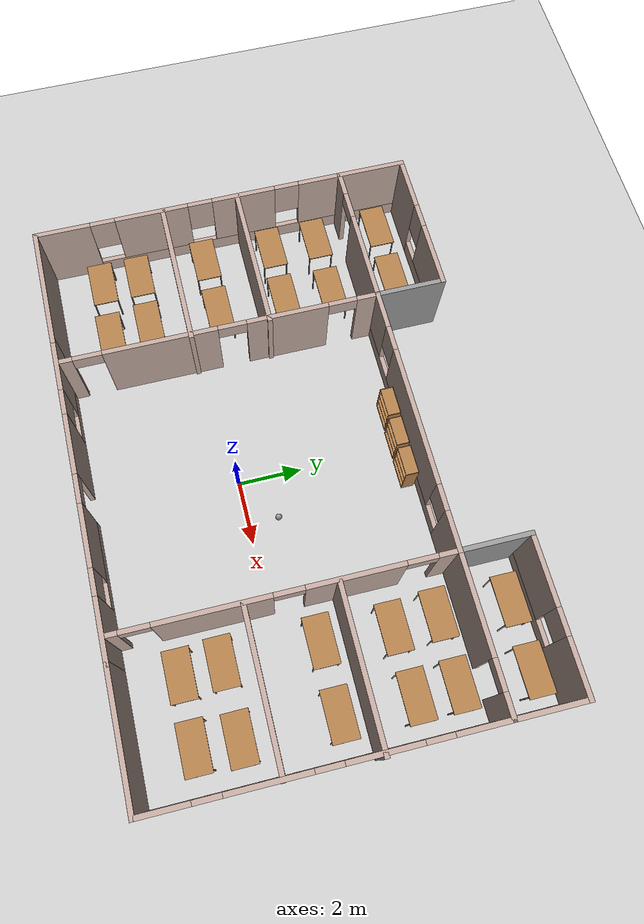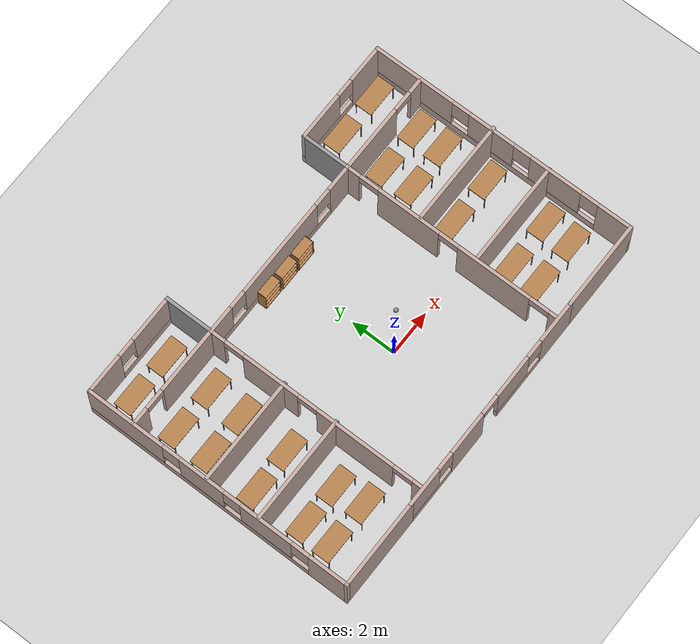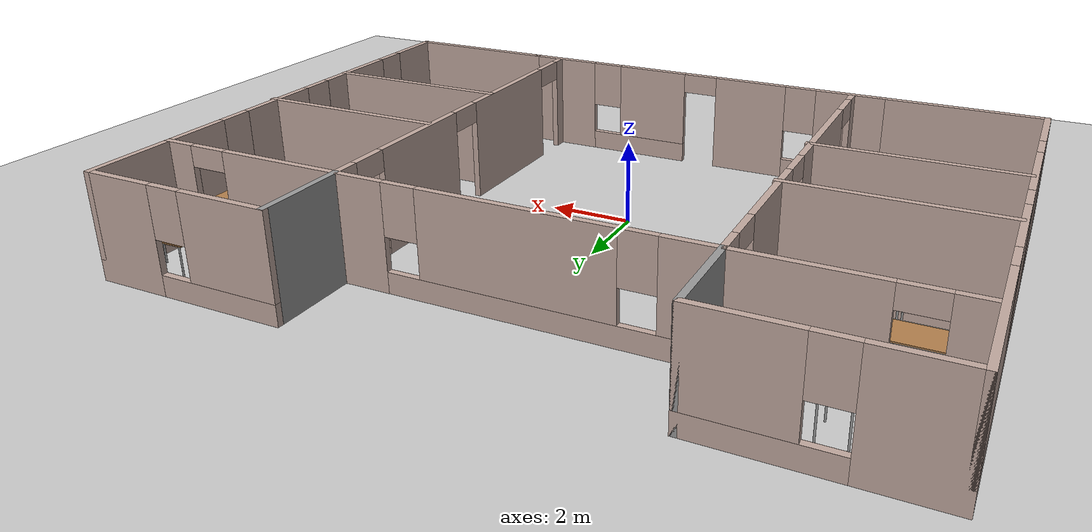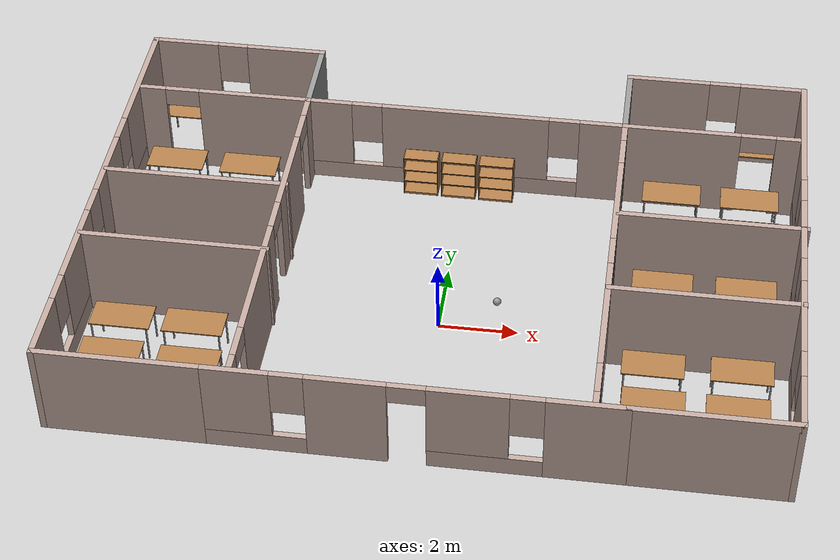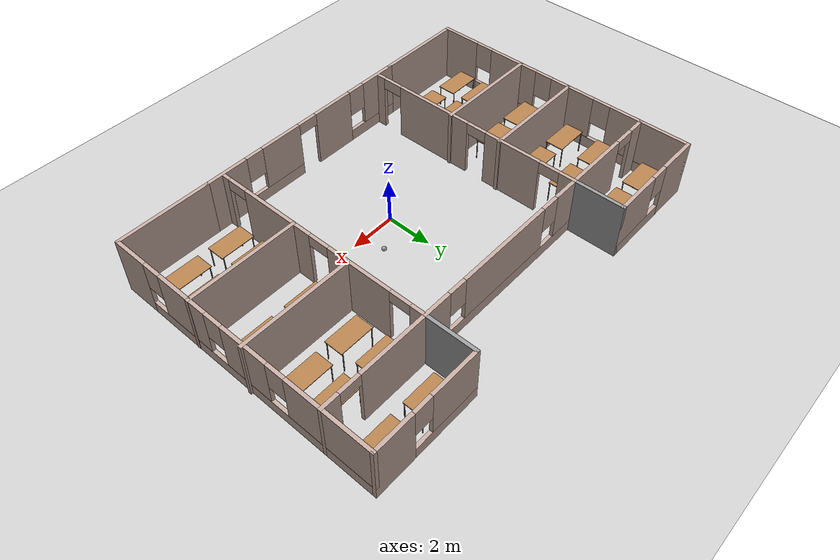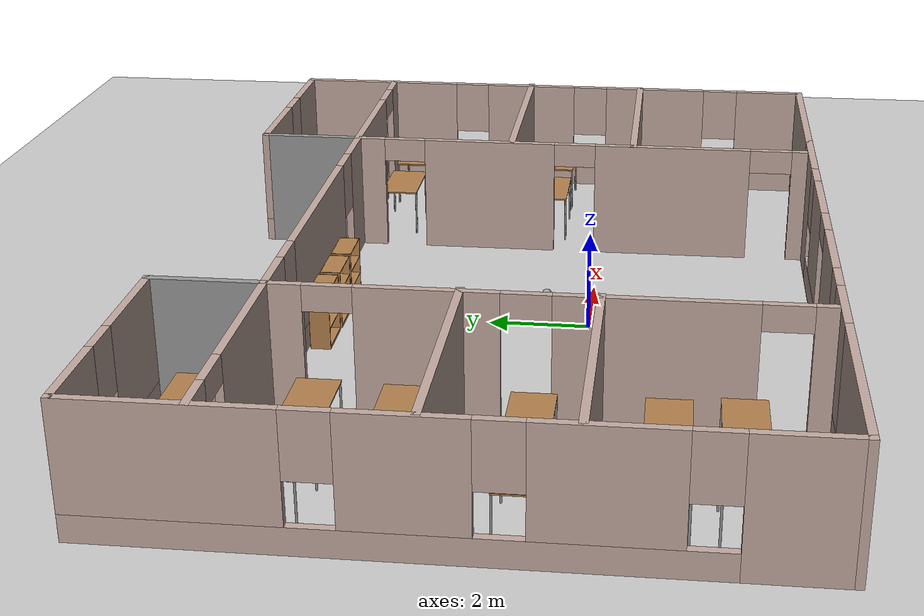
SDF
<sdf version="1.6">
 <world name="default">
  <light name="sun" type="directional">
   <pose>0 0 10 0 -0 0</pose>
   <diffuse>0.8 0.8 0.8 1</diffuse>
   <specular>0.2 0.2 0.2 1</specular>
   <attenuation>
    <range>1000</range>
    <constant>0.9</constant>
    <linear>0.01</linear>
    <quadratic>0.001</quadratic>
   </attenuation>
   <direction>-0.5 0.1 -0.9</direction>
  </light>
  <model name="ground_plane">
   <static>1</static>
   <link name="link">
    <collision name="collision">
     <geometry><plane><normal>0 0 1</normal><size>100 100</size></plane></geometry>
     <surface>
      <contact><collide_bitmask>65535</collide_bitmask></contact>
      <friction><ode><mu>100</mu><mu2>50</mu2></ode></friction>
     </surface>
    </collision>
    <visual name="visual">
     <cast_shadows>0</cast_shadows>
     <geometry><plane><normal>0 0 1</normal><size>100 100</size></plane></geometry>
     <material>
      <script><uri>file://media/materials/scripts/gazebo.material</uri><name>Gazebo/Grey</name></script>
     </material>
    </visual>
   </link>
  </model>
  <gravity>0 0 -9.8</gravity>
  <magnetic_field>6e-06 2.3e-05 -4.2e-05</magnetic_field>
  <atmosphere type="adiabatic"/>
  <physics name="default_physics" default="0" type="ode">
   <max_step_size>0.001</max_step_size>
   <real_time_factor>1</real_time_factor>
   <real_time_update_rate>1000</real_time_update_rate>
  </physics>
  <scene><ambient>0.4 0.4 0.4 1</ambient><background>0.7 0.7 0.7 1</background><shadows>1</shadows></scene>
  <spherical_coordinates>
   <surface_model>EARTH_WGS84</surface_model>
   <latitude_deg>0</latitude_deg>
   <longitude_deg>0</longitude_deg>
   <elevation>0</elevation>
   <heading_deg>0</heading_deg>
  </spherical_coordinates>
  <model name="Untitled">
   <pose>0.02249 1.505 0 0 -0 0</pose>
   <link name="Wall_33">
    <collision name="Wall_33_Collision">
     <geometry><box><size>4 0.15 2.5</size></box></geometry>
     <pose>0 0 1.25 0 -0 0</pose>
    </collision>
    <visual name="Wall_33_Visual">
     <pose>0 0 1.25 0 -0 0</pose>
     <geometry><box><size>4 0.15 2.5</size></box></geometry>
     <material>
      <script><uri>file://media/materials/scripts/gazebo.material</uri><name>Gazebo/Grey</name></script>
      <ambient>0.760784 0.662745 0.627451 1</ambient>
     </material>
     <meta><layer>0</layer></meta>
    </visual>
    <pose>-6.8875 -6.05 0 0 -0 3.14159</pose>
   </link>
   <link name="Wall_36">
    <pose>-8.8125 0 0 0 -0 1.5708</pose>
    <visual name="Wall_36_Visual_0">
     <pose>-5.21271 0 1.25 0 -0 0</pose>
     <geometry><box><size>1.82458 0.15 2.5</size></box></geometry>
     <material>
      <script><uri>file://media/materials/scripts/gazebo.material</uri><name>Gazebo/Grey</name></script>
      <ambient>0.760784 0.662745 0.627451 1</ambient>
     </material>
     <meta><layer>0</layer></meta>
    </visual>
    <collision name="Wall_36_Collision_0">
     <geometry><box><size>1.82458 0.15 2.5</size></box></geometry>
     <pose>-5.21271 0 1.25 0 -0 0</pose>
    </collision>
    <visual name="Wall_36_Visual_1">
     <pose>0.912289 0 0.25 0 -0 0</pose>
     <geometry><box><size>10.4254 0.15 0.5</size></box></geometry>
     <material>
      <script><uri>file://media/materials/scripts/gazebo.material</uri><name>Gazebo/Grey</name></script>
      <ambient>0.760784 0.662745 0.627451 1</ambient>
     </material>
     <meta><layer>0</layer></meta>
    </visual>
    <collision name="Wall_36_Collision_1">
     <geometry><box><size>10.4254 0.15 0.5</size></box></geometry>
     <pose>0.912289 0 0.25 0 -0 0</pose>
    </collision>
    <visual name="Wall_36_Visual_2">
     <pose>-2.30973 0 1.5 0 -0 0</pose>
     <geometry><box><size>2.38138 0.15 2</size></box></geometry>
     <material>
      <script><uri>file://media/materials/scripts/gazebo.material</uri><name>Gazebo/Grey</name></script>
      <ambient>0.760784 0.662745 0.627451 1</ambient>
     </material>
     <meta><layer>0</layer></meta>
    </visual>
    <collision name="Wall_36_Collision_2">
     <geometry><box><size>2.38138 0.15 2</size></box></geometry>
     <pose>-2.30973 0 1.5 0 -0 0</pose>
    </collision>
    <visual name="Wall_36_Visual_3">
     <pose>0.718703 0 1.5 0 -0 0</pose>
     <geometry><box><size>2.07548 0.15 2</size></box></geometry>
     <material>
      <script><uri>file://media/materials/scripts/gazebo.material</uri><name>Gazebo/Grey</name></script>
      <ambient>0.760784 0.662745 0.627451 1</ambient>
     </material>
     <meta><layer>0</layer></meta>
    </visual>
    <collision name="Wall_36_Collision_3">
     <geometry><box><size>2.07548 0.15 2</size></box></geometry>
     <pose>0.718703 0 1.5 0 -0 0</pose>
    </collision>
    <visual name="Wall_36_Visual_4">
     <pose>4.34072 0 1.5 0 -0 0</pose>
     <geometry><box><size>3.56856 0.15 2</size></box></geometry>
     <material>
      <script><uri>file://media/materials/scripts/gazebo.material</uri><name>Gazebo/Grey</name></script>
      <ambient>0.760784 0.662745 0.627451 1</ambient>
     </material>
     <meta><layer>0</layer></meta>
    </visual>
    <collision name="Wall_36_Collision_4">
     <geometry><box><size>3.56856 0.15 2</size></box></geometry>
     <pose>4.34072 0 1.5 0 -0 0</pose>
    </collision>
    <visual name="Wall_36_Visual_5">
     <pose>-3.90042 0 1.9 0 -0 0</pose>
     <geometry><box><size>0.8 0.15 1.2</size></box></geometry>
     <material>
      <script><uri>file://media/materials/scripts/gazebo.material</uri><name>Gazebo/Grey</name></script>
      <ambient>0.760784 0.662745 0.627451 1</ambient>
     </material>
     <meta><layer>0</layer></meta>
    </visual>
    <collision name="Wall_36_Collision_5">
     <geometry><box><size>0.8 0.15 1.2</size></box></geometry>
     <pose>-3.90042 0 1.9 0 -0 0</pose>
    </collision>
    <visual name="Wall_36_Visual_6">
     <pose>-0.719037 0 1.9 0 -0 0</pose>
     <geometry><box><size>0.8 0.15 1.2</size></box></geometry>
     <material>
      <script><uri>file://media/materials/scripts/gazebo.material</uri><name>Gazebo/Grey</name></script>
      <ambient>0.760784 0.662745 0.627451 1</ambient>
     </material>
     <meta><layer>0</layer></meta>
    </visual>
    <collision name="Wall_36_Collision_6">
     <geometry><box><size>0.8 0.15 1.2</size></box></geometry>
     <pose>-0.719037 0 1.9 0 -0 0</pose>
    </collision>
    <visual name="Wall_36_Visual_7">
     <pose>2.15644 0 1.9 0 -0 0</pose>
     <geometry><box><size>0.8 0.15 1.2</size></box></geometry>
     <material>
      <script><uri>file://media/materials/scripts/gazebo.material</uri><name>Gazebo/Grey</name></script>
      <ambient>0.760784 0.662745 0.627451 1</ambient>
     </material>
     <meta><layer>0</layer></meta>
    </visual>
    <collision name="Wall_36_Collision_7">
     <geometry><box><size>0.8 0.15 1.2</size></box></geometry>
     <pose>2.15644 0 1.9 0 -0 0</pose>
    </collision>
   </link>
   <link name="Wall_37">
    <pose>-6.5125 6.05 0 0 -0 0</pose>
    <visual name="Wall_37_Visual_0">
     <pose>-1.47007 0 1.25 0 -0 0</pose>
     <geometry><box><size>1.80987 0.15 2.5</size></box></geometry>
     <material>
      <script><uri>file://media/materials/scripts/gazebo.material</uri><name>Gazebo/Grey</name></script>
      <ambient>0.760784 0.662745 0.627451 1</ambient>
     </material>
     <meta><layer>0</layer></meta>
    </visual>
    <collision name="Wall_37_Collision_0">
     <geometry><box><size>1.80987 0.15 2.5</size></box></geometry>
     <pose>-1.47007 0 1.25 0 -0 0</pose>
    </collision>
    <visual name="Wall_37_Visual_1">
     <pose>0.904934 0 0.25 0 -0 0</pose>
     <geometry><box><size>2.94013 0.15 0.5</size></box></geometry>
     <material>
      <script><uri>file://media/materials/scripts/gazebo.material</uri><name>Gazebo/Grey</name></script>
      <ambient>0.760784 0.662745 0.627451 1</ambient>
     </material>
     <meta><layer>0</layer></meta>
    </visual>
    <collision name="Wall_37_Collision_1">
     <geometry><box><size>2.94013 0.15 0.5</size></box></geometry>
     <pose>0.904934 0 0.25 0 -0 0</pose>
    </collision>
    <visual name="Wall_37_Visual_2">
     <pose>1.30493 0 1.5 0 -0 0</pose>
     <geometry><box><size>2.14013 0.15 2</size></box></geometry>
     <material>
      <script><uri>file://media/materials/scripts/gazebo.material</uri><name>Gazebo/Grey</name></script>
      <ambient>0.760784 0.662745 0.627451 1</ambient>
     </material>
     <meta><layer>0</layer></meta>
    </visual>
    <collision name="Wall_37_Collision_2">
     <geometry><box><size>2.14013 0.15 2</size></box></geometry>
     <pose>1.30493 0 1.5 0 -0 0</pose>
    </collision>
    <visual name="Wall_37_Visual_3">
     <pose>-0.165132 0 1.9 0 -0 0</pose>
     <geometry><box><size>0.8 0.15 1.2</size></box></geometry>
     <material>
      <script><uri>file://media/materials/scripts/gazebo.material</uri><name>Gazebo/Grey</name></script>
      <ambient>0.760784 0.662745 0.627451 1</ambient>
     </material>
     <meta><layer>0</layer></meta>
    </visual>
    <collision name="Wall_37_Collision_3">
     <geometry><box><size>0.8 0.15 1.2</size></box></geometry>
     <pose>-0.165132 0 1.9 0 -0 0</pose>
    </collision>
   </link>
   <link name="Wall_40">
    <collision name="Wall_40_Collision">
     <geometry><box><size>4 0.15 2.5</size></box></geometry>
     <pose>0 0 1.25 0 -0 0</pose>
    </collision>
    <visual name="Wall_40_Visual">
     <pose>0 0 1.25 0 -0 0</pose>
     <geometry><box><size>4 0.15 2.5</size></box></geometry>
     <material>
      <script><uri>file://media/materials/scripts/gazebo.material</uri><name>Gazebo/Grey</name></script>
      <ambient>0.760784 0.662745 0.627451 1</ambient>
     </material>
     <meta><layer>0</layer></meta>
    </visual>
    <pose>6.8125 -6.05 0 0 -0 0</pose>
   </link>
   <link name="Wall_42">
    <pose>8.73751 0 0 0 -0 1.5708</pose>
    <visual name="Wall_42_Visual_0">
     <pose>-5.33507 0 1.25 0 -0 0</pose>
     <geometry><box><size>1.57986 0.15 2.5</size></box></geometry>
     <material>
      <script><uri>file://media/materials/scripts/gazebo.material</uri><name>Gazebo/Grey</name></script>
      <ambient>0.760784 0.662745 0.627451 1</ambient>
     </material>
     <meta><layer>0</layer></meta>
    </visual>
    <collision name="Wall_42_Collision_0">
     <geometry><box><size>1.57986 0.15 2.5</size></box></geometry>
     <pose>-5.33507 0 1.25 0 -0 0</pose>
    </collision>
    <visual name="Wall_42_Visual_1">
     <pose>0.789928 0 0.25 0 -0 0</pose>
     <geometry><box><size>10.6701 0.15 0.5</size></box></geometry>
     <material>
      <script><uri>file://media/materials/scripts/gazebo.material</uri><name>Gazebo/Grey</name></script>
      <ambient>0.760784 0.662745 0.627451 1</ambient>
     </material>
     <meta><layer>0</layer></meta>
    </visual>
    <collision name="Wall_42_Collision_1">
     <geometry><box><size>10.6701 0.15 0.5</size></box></geometry>
     <pose>0.789928 0 0.25 0 -0 0</pose>
    </collision>
    <visual name="Wall_42_Visual_2">
     <pose>-2.55445 0 1.5 0 -0 0</pose>
     <geometry><box><size>2.38138 0.15 2</size></box></geometry>
     <material>
      <script><uri>file://media/materials/scripts/gazebo.material</uri><name>Gazebo/Grey</name></script>
      <ambient>0.760784 0.662745 0.627451 1</ambient>
     </material>
     <meta><layer>0</layer></meta>
    </visual>
    <collision name="Wall_42_Collision_2">
     <geometry><box><size>2.38138 0.15 2</size></box></geometry>
     <pose>-2.55445 0 1.5 0 -0 0</pose>
    </collision>
    <visual name="Wall_42_Visual_3">
     <pose>0.504572 0 1.5 0 -0 0</pose>
     <geometry><box><size>2.13666 0.15 2</size></box></geometry>
     <material>
      <script><uri>file://media/materials/scripts/gazebo.material</uri><name>Gazebo/Grey</name></script>
      <ambient>0.760784 0.662745 0.627451 1</ambient>
     </material>
     <meta><layer>0</layer></meta>
    </visual>
    <collision name="Wall_42_Collision_3">
     <geometry><box><size>2.13666 0.15 2</size></box></geometry>
     <pose>0.504572 0 1.5 0 -0 0</pose>
    </collision>
    <visual name="Wall_42_Visual_4">
     <pose>4.24895 0 1.5 0 -0 0</pose>
     <geometry><box><size>3.7521 0.15 2</size></box></geometry>
     <material>
      <script><uri>file://media/materials/scripts/gazebo.material</uri><name>Gazebo/Grey</name></script>
      <ambient>0.760784 0.662745 0.627451 1</ambient>
     </material>
     <meta><layer>0</layer></meta>
    </visual>
    <collision name="Wall_42_Collision_4">
     <geometry><box><size>3.7521 0.15 2</size></box></geometry>
     <pose>4.24895 0 1.5 0 -0 0</pose>
    </collision>
    <visual name="Wall_42_Visual_5">
     <pose>-4.14514 0 1.9 0 -0 0</pose>
     <geometry><box><size>0.8 0.15 1.2</size></box></geometry>
     <material>
      <script><uri>file://media/materials/scripts/gazebo.material</uri><name>Gazebo/Grey</name></script>
      <ambient>0.760784 0.662745 0.627451 1</ambient>
     </material>
     <meta><layer>0</layer></meta>
    </visual>
    <collision name="Wall_42_Collision_5">
     <geometry><box><size>0.8 0.15 1.2</size></box></geometry>
     <pose>-4.14514 0 1.9 0 -0 0</pose>
    </collision>
    <visual name="Wall_42_Visual_6">
     <pose>-0.963759 0 1.9 0 -0 0</pose>
     <geometry><box><size>0.8 0.15 1.2</size></box></geometry>
     <material>
      <script><uri>file://media/materials/scripts/gazebo.material</uri><name>Gazebo/Grey</name></script>
      <ambient>0.760784 0.662745 0.627451 1</ambient>
     </material>
     <meta><layer>0</layer></meta>
    </visual>
    <collision name="Wall_42_Collision_6">
     <geometry><box><size>0.8 0.15 1.2</size></box></geometry>
     <pose>-0.963759 0 1.9 0 -0 0</pose>
    </collision>
    <visual name="Wall_42_Visual_7">
     <pose>1.9729 0 1.9 0 -0 0</pose>
     <geometry><box><size>0.8 0.15 1.2</size></box></geometry>
     <material>
      <script><uri>file://media/materials/scripts/gazebo.material</uri><name>Gazebo/Grey</name></script>
      <ambient>0.760784 0.662745 0.627451 1</ambient>
     </material>
     <meta><layer>0</layer></meta>
    </visual>
    <collision name="Wall_42_Collision_7">
     <geometry><box><size>0.8 0.15 1.2</size></box></geometry>
     <pose>1.9729 0 1.9 0 -0 0</pose>
    </collision>
   </link>
   <link name="Wall_44">
    <pose>6.4375 6.05 0 0 -0 3.14159</pose>
    <visual name="Wall_44_Visual_0">
     <pose>-1.4986 0 1.25 0 -0 0</pose>
     <geometry><box><size>1.75279 0.15 2.5</size></box></geometry>
     <material>
      <script><uri>file://media/materials/scripts/gazebo.material</uri><name>Gazebo/Grey</name></script>
      <ambient>0.760784 0.662745 0.627451 1</ambient>
     </material>
     <meta><layer>0</layer></meta>
    </visual>
    <collision name="Wall_44_Collision_0">
     <geometry><box><size>1.75279 0.15 2.5</size></box></geometry>
     <pose>-1.4986 0 1.25 0 -0 0</pose>
    </collision>
    <visual name="Wall_44_Visual_1">
     <pose>0.876396 0 0.25 0 -0 0</pose>
     <geometry><box><size>2.99721 0.15 0.5</size></box></geometry>
     <material>
      <script><uri>file://media/materials/scripts/gazebo.material</uri><name>Gazebo/Grey</name></script>
      <ambient>0.760784 0.662745 0.627451 1</ambient>
     </material>
     <meta><layer>0</layer></meta>
    </visual>
    <collision name="Wall_44_Collision_1">
     <geometry><box><size>2.99721 0.15 0.5</size></box></geometry>
     <pose>0.876396 0 0.25 0 -0 0</pose>
    </collision>
    <visual name="Wall_44_Visual_2">
     <pose>1.2764 0 1.5 0 -0 0</pose>
     <geometry><box><size>2.19721 0.15 2</size></box></geometry>
     <material>
      <script><uri>file://media/materials/scripts/gazebo.material</uri><name>Gazebo/Grey</name></script>
      <ambient>0.760784 0.662745 0.627451 1</ambient>
     </material>
     <meta><layer>0</layer></meta>
    </visual>
    <collision name="Wall_44_Collision_2">
     <geometry><box><size>2.19721 0.15 2</size></box></geometry>
     <pose>1.2764 0 1.5 0 -0 0</pose>
    </collision>
    <visual name="Wall_44_Visual_3">
     <pose>-0.222208 0 1.9 0 -0 0</pose>
     <geometry><box><size>0.8 0.15 1.2</size></box></geometry>
     <material>
      <script><uri>file://media/materials/scripts/gazebo.material</uri><name>Gazebo/Grey</name></script>
      <ambient>0.760784 0.662745 0.627451 1</ambient>
     </material>
     <meta><layer>0</layer></meta>
    </visual>
    <collision name="Wall_44_Collision_3">
     <geometry><box><size>0.8 0.15 1.2</size></box></geometry>
     <pose>-0.222208 0 1.9 0 -0 0</pose>
    </collision>
   </link>
   <link name="Wall_46">
    <collision name="Wall_46_Collision">
     <geometry><box><size>2.25 0.15 2.5</size></box></geometry>
     <pose>0 0 1.25 0 -0 0</pose>
    </collision>
    <visual name="Wall_46_Visual">
     <pose>0 0 1.25 0 -0 0</pose>
     <geometry><box><size>2.25 0.15 2.5</size></box></geometry>
     <material>
      <script><uri>file://media/materials/scripts/gazebo.material</uri><name>Gazebo/Grey</name></script>
      <ambient>1 1 1 1</ambient>
     </material>
     <meta><layer>0</layer></meta>
    </visual>
    <pose>4.1375 5 0 0 0 -1.5708</pose>
   </link>
   <link name="Wall_69">
    <pose>6.4375 3.95 0 0 -0 0</pose>
    <visual name="Wall_69_Visual_0">
     <pose>-0.842543 0 1.25 0 -0 0</pose>
     <geometry><box><size>3.06492 0.15 2.5</size></box></geometry>
     <material>
      <script><uri>file://media/materials/scripts/gazebo.material</uri><name>Gazebo/Grey</name></script>
      <ambient>0.760784 0.662745 0.627451 1</ambient>
     </material>
     <meta><layer>0</layer></meta>
    </visual>
    <collision name="Wall_69_Collision_0">
     <geometry><box><size>3.06492 0.15 2.5</size></box></geometry>
     <pose>-0.842543 0 1.25 0 -0 0</pose>
    </collision>
    <visual name="Wall_69_Visual_1">
     <pose>1.98246 0 1.25 0 -0 0</pose>
     <geometry><box><size>0.785085 0.15 2.5</size></box></geometry>
     <material>
      <script><uri>file://media/materials/scripts/gazebo.material</uri><name>Gazebo/Grey</name></script>
      <ambient>0.760784 0.662745 0.627451 1</ambient>
     </material>
     <meta><layer>0</layer></meta>
    </visual>
    <collision name="Wall_69_Collision_1">
     <geometry><box><size>0.785085 0.15 2.5</size></box></geometry>
     <pose>1.98246 0 1.25 0 -0 0</pose>
    </collision>
    <visual name="Wall_69_Visual_2">
     <pose>1.13992 0 2.25 0 -0 0</pose>
     <geometry><box><size>0.9 0.15 0.5</size></box></geometry>
     <material>
      <script><uri>file://media/materials/scripts/gazebo.material</uri><name>Gazebo/Grey</name></script>
      <ambient>0.760784 0.662745 0.627451 1</ambient>
     </material>
     <meta><layer>0</layer></meta>
    </visual>
    <collision name="Wall_69_Collision_2">
     <geometry><box><size>0.9 0.15 0.5</size></box></geometry>
     <pose>1.13992 0 2.25 0 -0 0</pose>
    </collision>
   </link>
   <link name="Wall_73">
    <pose>-0.037495 3.95 0 0 -0 3.14159</pose>
    <visual name="Wall_73_Visual_0">
     <pose>-3.62406 0 1.25 0 -0 0</pose>
     <geometry><box><size>1.25188 0.15 2.5</size></box></geometry>
     <material>
      <script><uri>file://media/materials/scripts/gazebo.material</uri><name>Gazebo/Grey</name></script>
      <ambient>0.760784 0.662745 0.627451 1</ambient>
     </material>
     <meta><layer>0</layer></meta>
    </visual>
    <collision name="Wall_73_Collision_0">
     <geometry><box><size>1.25188 0.15 2.5</size></box></geometry>
     <pose>-3.62406 0 1.25 0 -0 0</pose>
    </collision>
    <visual name="Wall_73_Visual_1">
     <pose>0.625941 0 0.25 0 -0 0</pose>
     <geometry><box><size>7.24812 0.15 0.5</size></box></geometry>
     <material>
      <script><uri>file://media/materials/scripts/gazebo.material</uri><name>Gazebo/Grey</name></script>
      <ambient>0.760784 0.662745 0.627451 1</ambient>
     </material>
     <meta><layer>0</layer></meta>
    </visual>
    <collision name="Wall_73_Collision_1">
     <geometry><box><size>7.24812 0.15 0.5</size></box></geometry>
     <pose>0.625941 0 0.25 0 -0 0</pose>
    </collision>
    <visual name="Wall_73_Visual_2">
     <pose>0.002052 0 1.5 0 -0 0</pose>
     <geometry><box><size>4.40034 0.15 2</size></box></geometry>
     <material>
      <script><uri>file://media/materials/scripts/gazebo.material</uri><name>Gazebo/Grey</name></script>
      <ambient>0.760784 0.662745 0.627451 1</ambient>
     </material>
     <meta><layer>0</layer></meta>
    </visual>
    <collision name="Wall_73_Collision_2">
     <geometry><box><size>4.40034 0.15 2</size></box></geometry>
     <pose>0.002052 0 1.5 0 -0 0</pose>
    </collision>
    <visual name="Wall_73_Visual_3">
     <pose>3.62611 0 1.5 0 -0 0</pose>
     <geometry><box><size>1.24778 0.15 2</size></box></geometry>
     <material>
      <script><uri>file://media/materials/scripts/gazebo.material</uri><name>Gazebo/Grey</name></script>
      <ambient>0.760784 0.662745 0.627451 1</ambient>
     </material>
     <meta><layer>0</layer></meta>
    </visual>
    <collision name="Wall_73_Collision_3">
     <geometry><box><size>1.24778 0.15 2</size></box></geometry>
     <pose>3.62611 0 1.5 0 -0 0</pose>
    </collision>
    <visual name="Wall_73_Visual_4">
     <pose>-2.59812 0 1.9 0 -0 0</pose>
     <geometry><box><size>0.8 0.15 1.2</size></box></geometry>
     <material>
      <script><uri>file://media/materials/scripts/gazebo.material</uri><name>Gazebo/Grey</name></script>
      <ambient>0.760784 0.662745 0.627451 1</ambient>
     </material>
     <meta><layer>0</layer></meta>
    </visual>
    <collision name="Wall_73_Collision_4">
     <geometry><box><size>0.8 0.15 1.2</size></box></geometry>
     <pose>-2.59812 0 1.9 0 -0 0</pose>
    </collision>
    <visual name="Wall_73_Visual_5">
     <pose>2.60222 0 1.9 0 -0 0</pose>
     <geometry><box><size>0.8 0.15 1.2</size></box></geometry>
     <material>
      <script><uri>file://media/materials/scripts/gazebo.material</uri><name>Gazebo/Grey</name></script>
      <ambient>0.760784 0.662745 0.627451 1</ambient>
     </material>
     <meta><layer>0</layer></meta>
    </visual>
    <collision name="Wall_73_Collision_5">
     <geometry><box><size>0.8 0.15 1.2</size></box></geometry>
     <pose>2.60222 0 1.9 0 -0 0</pose>
    </collision>
   </link>
   <link name="Wall_74">
    <collision name="Wall_74_Collision">
     <geometry><box><size>2.25 0.15 2.5</size></box></geometry>
     <pose>0 0 1.25 0 -0 0</pose>
    </collision>
    <visual name="Wall_74_Visual">
     <pose>0 0 1.25 0 -0 0</pose>
     <geometry><box><size>2.25 0.15 2.5</size></box></geometry>
     <material>
      <script><uri>file://media/materials/scripts/gazebo.material</uri><name>Gazebo/Grey</name></script>
      <ambient>1 1 1 1</ambient>
     </material>
     <meta><layer>0</layer></meta>
    </visual>
    <pose>-4.21249 5 0 0 -0 1.5708</pose>
   </link>
   <link name="Wall_76">
    <pose>-6.5125 3.95 0 0 -0 3.14159</pose>
    <visual name="Wall_76_Visual_0">
     <pose>-0.871081 0 1.25 0 -0 0</pose>
     <geometry><box><size>3.00784 0.15 2.5</size></box></geometry>
     <material>
      <script><uri>file://media/materials/scripts/gazebo.material</uri><name>Gazebo/Grey</name></script>
      <ambient>0.760784 0.662745 0.627451 1</ambient>
     </material>
     <meta><layer>0</layer></meta>
    </visual>
    <collision name="Wall_76_Collision_0">
     <geometry><box><size>3.00784 0.15 2.5</size></box></geometry>
     <pose>-0.871081 0 1.25 0 -0 0</pose>
    </collision>
    <visual name="Wall_76_Visual_1">
     <pose>1.95392 0 1.25 0 -0 0</pose>
     <geometry><box><size>0.842161 0.15 2.5</size></box></geometry>
     <material>
      <script><uri>file://media/materials/scripts/gazebo.material</uri><name>Gazebo/Grey</name></script>
      <ambient>0.760784 0.662745 0.627451 1</ambient>
     </material>
     <meta><layer>0</layer></meta>
    </visual>
    <collision name="Wall_76_Collision_1">
     <geometry><box><size>0.842161 0.15 2.5</size></box></geometry>
     <pose>1.95392 0 1.25 0 -0 0</pose>
    </collision>
    <visual name="Wall_76_Visual_2">
     <pose>1.08284 0 2.25 0 -0 0</pose>
     <geometry><box><size>0.9 0.15 0.5</size></box></geometry>
     <material>
      <script><uri>file://media/materials/scripts/gazebo.material</uri><name>Gazebo/Grey</name></script>
      <ambient>0.760784 0.662745 0.627451 1</ambient>
     </material>
     <meta><layer>0</layer></meta>
    </visual>
    <collision name="Wall_76_Collision_2">
     <geometry><box><size>0.9 0.15 0.5</size></box></geometry>
     <pose>1.08284 0 2.25 0 -0 0</pose>
    </collision>
   </link>
   <link name="Wall_8">
    <pose>-0.037495 -6.05 0 0 -0 3.14159</pose>
    <visual name="Wall_8_Visual_0">
     <pose>-4.02965 0 1.25 0 -0 0</pose>
     <geometry><box><size>1.9407 0.15 2.5</size></box></geometry>
     <material>
      <script><uri>file://media/materials/scripts/gazebo.material</uri><name>Gazebo/Grey</name></script>
      <ambient>0.760784 0.662745 0.627451 1</ambient>
     </material>
     <meta><layer>0</layer></meta>
    </visual>
    <collision name="Wall_8_Collision_0">
     <geometry><box><size>1.9407 0.15 2.5</size></box></geometry>
     <pose>-4.02965 0 1.25 0 -0 0</pose>
    </collision>
    <visual name="Wall_8_Visual_1">
     <pose>1.49538 0 1.25 0 -0 0</pose>
     <geometry><box><size>1.90312 0.15 2.5</size></box></geometry>
     <material>
      <script><uri>file://media/materials/scripts/gazebo.material</uri><name>Gazebo/Grey</name></script>
      <ambient>0.760784 0.662745 0.627451 1</ambient>
     </material>
     <meta><layer>0</layer></meta>
    </visual>
    <collision name="Wall_8_Collision_1">
     <geometry><box><size>1.90312 0.15 2.5</size></box></geometry>
     <pose>1.49538 0 1.25 0 -0 0</pose>
    </collision>
    <visual name="Wall_8_Visual_2">
     <pose>-1.70774 0 0.25 0 -0 0</pose>
     <geometry><box><size>2.70312 0.15 0.5</size></box></geometry>
     <material>
      <script><uri>file://media/materials/scripts/gazebo.material</uri><name>Gazebo/Grey</name></script>
      <ambient>0.760784 0.662745 0.627451 1</ambient>
     </material>
     <meta><layer>0</layer></meta>
    </visual>
    <collision name="Wall_8_Collision_2">
     <geometry><box><size>2.70312 0.15 0.5</size></box></geometry>
     <pose>-1.70774 0 0.25 0 -0 0</pose>
    </collision>
    <visual name="Wall_8_Visual_3">
     <pose>3.72347 0 0.25 0 -0 0</pose>
     <geometry><box><size>2.55306 0.15 0.5</size></box></geometry>
     <material>
      <script><uri>file://media/materials/scripts/gazebo.material</uri><name>Gazebo/Grey</name></script>
      <ambient>0.760784 0.662745 0.627451 1</ambient>
     </material>
     <meta><layer>0</layer></meta>
    </visual>
    <collision name="Wall_8_Collision_3">
     <geometry><box><size>2.55306 0.15 0.5</size></box></geometry>
     <pose>3.72347 0 0.25 0 -0 0</pose>
    </collision>
    <visual name="Wall_8_Visual_4">
     <pose>-1.30774 0 1.5 0 -0 0</pose>
     <geometry><box><size>1.90312 0.15 2</size></box></geometry>
     <material>
      <script><uri>file://media/materials/scripts/gazebo.material</uri><name>Gazebo/Grey</name></script>
      <ambient>0.760784 0.662745 0.627451 1</ambient>
     </material>
     <meta><layer>0</layer></meta>
    </visual>
    <collision name="Wall_8_Collision_4">
     <geometry><box><size>1.90312 0.15 2</size></box></geometry>
     <pose>-1.30774 0 1.5 0 -0 0</pose>
    </collision>
    <visual name="Wall_8_Visual_5">
     <pose>-1.30774 0 1.5 0 -0 0</pose>
     <geometry><box><size>1.90312 0.15 2</size></box></geometry>
     <material>
      <script><uri>file://media/materials/scripts/gazebo.material</uri><name>Gazebo/Grey</name></script>
      <ambient>0.760784 0.662745 0.627451 1</ambient>
     </material>
     <meta><layer>0</layer></meta>
    </visual>
    <collision name="Wall_8_Collision_5">
     <geometry><box><size>1.90312 0.15 2</size></box></geometry>
     <pose>-1.30774 0 1.5 0 -0 0</pose>
    </collision>
    <visual name="Wall_8_Visual_6">
     <pose>4.12347 0 1.5 0 -0 0</pose>
     <geometry><box><size>1.75306 0.15 2</size></box></geometry>
     <material>
      <script><uri>file://media/materials/scripts/gazebo.material</uri><name>Gazebo/Grey</name></script>
      <ambient>0.760784 0.662745 0.627451 1</ambient>
     </material>
     <meta><layer>0</layer></meta>
    </visual>
    <collision name="Wall_8_Collision_6">
     <geometry><box><size>1.75306 0.15 2</size></box></geometry>
     <pose>4.12347 0 1.5 0 -0 0</pose>
    </collision>
    <visual name="Wall_8_Visual_7">
     <pose>-2.6593 0 1.9 0 -0 0</pose>
     <geometry><box><size>0.8 0.15 1.2</size></box></geometry>
     <material>
      <script><uri>file://media/materials/scripts/gazebo.material</uri><name>Gazebo/Grey</name></script>
      <ambient>0.760784 0.662745 0.627451 1</ambient>
     </material>
     <meta><layer>0</layer></meta>
    </visual>
    <collision name="Wall_8_Collision_7">
     <geometry><box><size>0.8 0.15 1.2</size></box></geometry>
     <pose>-2.6593 0 1.9 0 -0 0</pose>
    </collision>
    <visual name="Wall_8_Visual_8">
     <pose>2.84694 0 1.9 0 -0 0</pose>
     <geometry><box><size>0.8 0.15 1.2</size></box></geometry>
     <material>
      <script><uri>file://media/materials/scripts/gazebo.material</uri><name>Gazebo/Grey</name></script>
      <ambient>0.760784 0.662745 0.627451 1</ambient>
     </material>
     <meta><layer>0</layer></meta>
    </visual>
    <collision name="Wall_8_Collision_8">
     <geometry><box><size>0.8 0.15 1.2</size></box></geometry>
     <pose>2.84694 0 1.9 0 -0 0</pose>
    </collision>
    <visual name="Wall_8_Visual_9">
     <pose>0.093823 0 2.25 0 -0 0</pose>
     <geometry><box><size>0.9 0.15 0.5</size></box></geometry>
     <material>
      <script><uri>file://media/materials/scripts/gazebo.material</uri><name>Gazebo/Grey</name></script>
      <ambient>0.760784 0.662745 0.627451 1</ambient>
     </material>
     <meta><layer>0</layer></meta>
    </visual>
    <collision name="Wall_8_Collision_9">
     <geometry><box><size>0.9 0.15 0.5</size></box></geometry>
     <pose>0.093823 0 2.25 0 -0 0</pose>
    </collision>
    <visual name="Wall_8_Visual_10">
     <pose>0.093823 0 2.25 0 -0 0</pose>
     <geometry><box><size>0.9 0.15 0.5</size></box></geometry>
     <material>
      <script><uri>file://media/materials/scripts/gazebo.material</uri><name>Gazebo/Grey</name></script>
      <ambient>0.760784 0.662745 0.627451 1</ambient>
     </material>
     <meta><layer>0</layer></meta>
    </visual>
    <collision name="Wall_8_Collision_10">
     <geometry><box><size>0.9 0.15 0.5</size></box></geometry>
     <pose>0.093823 0 2.25 0 -0 0</pose>
    </collision>
   </link>
   <link name="Wall_83">
    <pose>-4.21249 -0.975 0 0 0 -1.5708</pose>
    <visual name="Wall_83_Visual_0">
     <pose>-4.62721 0 1.25 0 -0 0</pose>
     <geometry><box><size>0.745571 0.15 2.5</size></box></geometry>
     <material>
      <script><uri>file://media/materials/scripts/gazebo.material</uri><name>Gazebo/Grey</name></script>
      <ambient>0.760784 0.662745 0.627451 1</ambient>
     </material>
     <meta><layer>0</layer></meta>
    </visual>
    <collision name="Wall_83_Collision_0">
     <geometry><box><size>0.745571 0.15 2.5</size></box></geometry>
     <pose>-4.62721 0 1.25 0 -0 0</pose>
    </collision>
    <visual name="Wall_83_Visual_1">
     <pose>-2.06079 0 1.25 0 -0 0</pose>
     <geometry><box><size>2.58729 0.15 2.5</size></box></geometry>
     <material>
      <script><uri>file://media/materials/scripts/gazebo.material</uri><name>Gazebo/Grey</name></script>
      <ambient>0.760784 0.662745 0.627451 1</ambient>
     </material>
     <meta><layer>0</layer></meta>
    </visual>
    <collision name="Wall_83_Collision_1">
     <geometry><box><size>2.58729 0.15 2.5</size></box></geometry>
     <pose>-2.06079 0 1.25 0 -0 0</pose>
    </collision>
    <visual name="Wall_83_Visual_2">
     <pose>1.91594 0 1.25 0 -0 0</pose>
     <geometry><box><size>3.56617 0.15 2.5</size></box></geometry>
     <material>
      <script><uri>file://media/materials/scripts/gazebo.material</uri><name>Gazebo/Grey</name></script>
      <ambient>0.760784 0.662745 0.627451 1</ambient>
     </material>
     <meta><layer>0</layer></meta>
    </visual>
    <collision name="Wall_83_Collision_2">
     <geometry><box><size>3.56617 0.15 2.5</size></box></geometry>
     <pose>1.91594 0 1.25 0 -0 0</pose>
    </collision>
    <visual name="Wall_83_Visual_3">
     <pose>4.79952 0 1.25 0 -0 0</pose>
     <geometry><box><size>0.40097 0.15 2.5</size></box></geometry>
     <material>
      <script><uri>file://media/materials/scripts/gazebo.material</uri><name>Gazebo/Grey</name></script>
      <ambient>0.760784 0.662745 0.627451 1</ambient>
     </material>
     <meta><layer>0</layer></meta>
    </visual>
    <collision name="Wall_83_Collision_3">
     <geometry><box><size>0.40097 0.15 2.5</size></box></geometry>
     <pose>4.79952 0 1.25 0 -0 0</pose>
    </collision>
    <visual name="Wall_83_Visual_4">
     <pose>-3.80443 0 2.25 0 -0 0</pose>
     <geometry><box><size>0.9 0.15 0.5</size></box></geometry>
     <material>
      <script><uri>file://media/materials/scripts/gazebo.material</uri><name>Gazebo/Grey</name></script>
      <ambient>0.760784 0.662745 0.627451 1</ambient>
     </material>
     <meta><layer>0</layer></meta>
    </visual>
    <collision name="Wall_83_Collision_4">
     <geometry><box><size>0.9 0.15 0.5</size></box></geometry>
     <pose>-3.80443 0 2.25 0 -0 0</pose>
    </collision>
    <visual name="Wall_83_Visual_5">
     <pose>-0.317143 0 2.25 0 -0 0</pose>
     <geometry><box><size>0.9 0.15 0.5</size></box></geometry>
     <material>
      <script><uri>file://media/materials/scripts/gazebo.material</uri><name>Gazebo/Grey</name></script>
      <ambient>0.760784 0.662745 0.627451 1</ambient>
     </material>
     <meta><layer>0</layer></meta>
    </visual>
    <collision name="Wall_83_Collision_5">
     <geometry><box><size>0.9 0.15 0.5</size></box></geometry>
     <pose>-0.317143 0 2.25 0 -0 0</pose>
    </collision>
    <visual name="Wall_83_Visual_6">
     <pose>4.14903 0 2.25 0 -0 0</pose>
     <geometry><box><size>0.9 0.15 0.5</size></box></geometry>
     <material>
      <script><uri>file://media/materials/scripts/gazebo.material</uri><name>Gazebo/Grey</name></script>
      <ambient>0.760784 0.662745 0.627451 1</ambient>
     </material>
     <meta><layer>0</layer></meta>
    </visual>
    <collision name="Wall_83_Collision_6">
     <geometry><box><size>0.9 0.15 0.5</size></box></geometry>
     <pose>4.14903 0 2.25 0 -0 0</pose>
    </collision>
   </link>
   <link name="Wall_85">
    <pose>4.1375 -0.975 0 0 0 -1.5708</pose>
    <visual name="Wall_85_Visual_0">
     <pose>-4.6578 0 1.25 0 -0 0</pose>
     <geometry><box><size>0.684391 0.15 2.5</size></box></geometry>
     <material>
      <script><uri>file://media/materials/scripts/gazebo.material</uri><name>Gazebo/Grey</name></script>
      <ambient>0.760784 0.662745 0.627451 1</ambient>
     </material>
     <meta><layer>0</layer></meta>
    </visual>
    <collision name="Wall_85_Collision_0">
     <geometry><box><size>0.684391 0.15 2.5</size></box></geometry>
     <pose>-4.6578 0 1.25 0 -0 0</pose>
    </collision>
    <visual name="Wall_85_Visual_1">
     <pose>-1.96901 0 1.25 0 -0 0</pose>
     <geometry><box><size>2.89319 0.15 2.5</size></box></geometry>
     <material>
      <script><uri>file://media/materials/scripts/gazebo.material</uri><name>Gazebo/Grey</name></script>
      <ambient>0.760784 0.662745 0.627451 1</ambient>
     </material>
     <meta><layer>0</layer></meta>
    </visual>
    <collision name="Wall_85_Collision_1">
     <geometry><box><size>2.89319 0.15 2.5</size></box></geometry>
     <pose>-1.96901 0 1.25 0 -0 0</pose>
    </collision>
    <visual name="Wall_85_Visual_2">
     <pose>2.06889 0 1.25 0 -0 0</pose>
     <geometry><box><size>3.38263 0.15 2.5</size></box></geometry>
     <material>
      <script><uri>file://media/materials/scripts/gazebo.material</uri><name>Gazebo/Grey</name></script>
      <ambient>0.760784 0.662745 0.627451 1</ambient>
     </material>
     <meta><layer>0</layer></meta>
    </visual>
    <collision name="Wall_85_Collision_2">
     <geometry><box><size>3.38263 0.15 2.5</size></box></geometry>
     <pose>2.06889 0 1.25 0 -0 0</pose>
    </collision>
    <visual name="Wall_85_Visual_3">
     <pose>4.8301 0 1.25 0 -0 0</pose>
     <geometry><box><size>0.339789 0.15 2.5</size></box></geometry>
     <material>
      <script><uri>file://media/materials/scripts/gazebo.material</uri><name>Gazebo/Grey</name></script>
      <ambient>0.760784 0.662745 0.627451 1</ambient>
     </material>
     <meta><layer>0</layer></meta>
    </visual>
    <collision name="Wall_85_Collision_3">
     <geometry><box><size>0.339789 0.15 2.5</size></box></geometry>
     <pose>4.8301 0 1.25 0 -0 0</pose>
    </collision>
    <visual name="Wall_85_Visual_4">
     <pose>-3.86561 0 2.25 0 -0 0</pose>
     <geometry><box><size>0.9 0.15 0.5</size></box></geometry>
     <material>
      <script><uri>file://media/materials/scripts/gazebo.material</uri><name>Gazebo/Grey</name></script>
      <ambient>0.760784 0.662745 0.627451 1</ambient>
     </material>
     <meta><layer>0</layer></meta>
    </visual>
    <collision name="Wall_85_Collision_4">
     <geometry><box><size>0.9 0.15 0.5</size></box></geometry>
     <pose>-3.86561 0 2.25 0 -0 0</pose>
    </collision>
    <visual name="Wall_85_Visual_5">
     <pose>-0.072421 0 2.25 0 -0 0</pose>
     <geometry><box><size>0.9 0.15 0.5</size></box></geometry>
     <material>
      <script><uri>file://media/materials/scripts/gazebo.material</uri><name>Gazebo/Grey</name></script>
      <ambient>0.760784 0.662745 0.627451 1</ambient>
     </material>
     <meta><layer>0</layer></meta>
    </visual>
    <collision name="Wall_85_Collision_5">
     <geometry><box><size>0.9 0.15 0.5</size></box></geometry>
     <pose>-0.072421 0 2.25 0 -0 0</pose>
    </collision>
    <visual name="Wall_85_Visual_6">
     <pose>4.21021 0 2.25 0 -0 0</pose>
     <geometry><box><size>0.9 0.15 0.5</size></box></geometry>
     <material>
      <script><uri>file://media/materials/scripts/gazebo.material</uri><name>Gazebo/Grey</name></script>
      <ambient>0.760784 0.662745 0.627451 1</ambient>
     </material>
     <meta><layer>0</layer></meta>
    </visual>
    <collision name="Wall_85_Collision_6">
     <geometry><box><size>0.9 0.15 0.5</size></box></geometry>
     <pose>4.21021 0 2.25 0 -0 0</pose>
    </collision>
   </link>
   <link name="Wall_89">
    <collision name="Wall_89_Collision">
     <geometry><box><size>4.75 0.15 2.5</size></box></geometry>
     <pose>0 0 1.25 0 -0 0</pose>
    </collision>
    <visual name="Wall_89_Visual">
     <pose>0 0 1.25 0 -0 0</pose>
     <geometry><box><size>4.75 0.15 2.5</size></box></geometry>
     <material>
      <script><uri>file://media/materials/scripts/gazebo.material</uri><name>Gazebo/Grey</name></script>
      <ambient>0.760784 0.662745 0.627451 1</ambient>
     </material>
     <meta><layer>0</layer></meta>
    </visual>
    <pose>-6.45776 0.504572 0 0 -0 0</pose>
   </link>
   <link name="Wall_91">
    <collision name="Wall_91_Collision">
     <geometry><box><size>4.75 0.15 2.5</size></box></geometry>
     <pose>0 0 1.25 0 -0 0</pose>
    </collision>
    <visual name="Wall_91_Visual">
     <pose>0 0 1.25 0 -0 0</pose>
     <geometry><box><size>4.75 0.15 2.5</size></box></geometry>
     <material>
      <script><uri>file://media/materials/scripts/gazebo.material</uri><name>Gazebo/Grey</name></script>
      <ambient>0.760784 0.662745 0.627451 1</ambient>
     </material>
     <meta><layer>0</layer></meta>
    </visual>
    <pose>-6.45776 -1.94265 0 0 -0 0</pose>
   </link>
   <link name="Wall_93">
    <collision name="Wall_93_Collision">
     <geometry><box><size>4.75 0.15 2.5</size></box></geometry>
     <pose>0 0 1.25 0 -0 0</pose>
    </collision>
    <visual name="Wall_93_Visual">
     <pose>0 0 1.25 0 -0 0</pose>
     <geometry><box><size>4.75 0.15 2.5</size></box></geometry>
     <material>
      <script><uri>file://media/materials/scripts/gazebo.material</uri><name>Gazebo/Grey</name></script>
      <ambient>0.760784 0.662745 0.627451 1</ambient>
     </material>
     <meta><layer>0</layer></meta>
    </visual>
    <pose>6.5125 0.504572 0 0 -0 0</pose>
   </link>
   <link name="Wall_95">
    <collision name="Wall_95_Collision">
     <geometry><box><size>4.75 0.15 2.5</size></box></geometry>
     <pose>0 0 1.25 0 -0 0</pose>
    </collision>
    <visual name="Wall_95_Visual">
     <pose>0 0 1.25 0 -0 0</pose>
     <geometry><box><size>4.75 0.15 2.5</size></box></geometry>
     <material>
      <script><uri>file://media/materials/scripts/gazebo.material</uri><name>Gazebo/Grey</name></script>
      <ambient>0.760784 0.662745 0.627451 1</ambient>
     </material>
     <meta><layer>0</layer></meta>
    </visual>
    <pose>6.45131 -2.18737 0 0 -0 0</pose>
   </link>
   <static>1</static>
  </model>
  <model name="bookshelf">
   <static>1</static>
   <link name="link">
    <inertial><mass>1</mass></inertial>
    <collision name="back">
     <pose>0 0.005 0.6 0 -0 0</pose>
     <geometry><box><size>0.9 0.01 1.2</size></box></geometry>
    </collision>
    <visual name="visual1">
     <pose>0 0.005 0.6 0 -0 0</pose>
     <geometry><box><size>0.9 0.01 1.2</size></box></geometry>
     <material>
      <script><uri>file://media/materials/scripts/gazebo.material</uri><name>Gazebo/Wood</name></script>
     </material>
    </visual>
    <collision name="left_side">
     <pose>0.45 -0.195 0.6 0 -0 0</pose>
     <geometry><box><size>0.02 0.4 1.2</size></box></geometry>
    </collision>
    <visual name="visual2">
     <pose>0.45 -0.195 0.6 0 -0 0</pose>
     <geometry><box><size>0.02 0.4 1.2</size></box></geometry>
     <material>
      <script><uri>file://media/materials/scripts/gazebo.material</uri><name>Gazebo/Wood</name></script>
     </material>
    </visual>
    <collision name="right_side">
     <pose>-0.45 -0.195 0.6 0 -0 0</pose>
     <geometry><box><size>0.02 0.4 1.2</size></box></geometry>
    </collision>
    <visual name="visual3">
     <pose>-0.45 -0.195 0.6 0 -0 0</pose>
     <geometry><box><size>0.02 0.4 1.2</size></box></geometry>
     <material>
      <script><uri>file://media/materials/scripts/gazebo.material</uri><name>Gazebo/Wood</name></script>
     </material>
    </visual>
    <collision name="bottom">
     <pose>0 -0.195 0.03 0 -0 0</pose>
     <geometry><box><size>0.88 0.4 0.06</size></box></geometry>
    </collision>
    <visual name="visual4">
     <pose>0 -0.195 0.03 0 -0 0</pose>
     <geometry><box><size>0.88 0.4 0.06</size></box></geometry>
     <material>
      <script><uri>file://media/materials/scripts/gazebo.material</uri><name>Gazebo/Wood</name></script>
     </material>
    </visual>
    <collision name="top">
     <pose>0 -0.195 1.19 0 -0 0</pose>
     <geometry><box><size>0.88 0.4 0.02</size></box></geometry>
    </collision>
    <visual name="visual5">
     <pose>0 -0.195 1.19 0 -0 0</pose>
     <geometry><box><size>0.88 0.4 0.02</size></box></geometry>
     <material>
      <script><uri>file://media/materials/scripts/gazebo.material</uri><name>Gazebo/Wood</name></script>
     </material>
    </visual>
    <collision name="low_shelf">
     <pose>0 -0.195 0.43 0 -0 0</pose>
     <geometry><box><size>0.88 0.4 0.02</size></box></geometry>
    </collision>
    <visual name="visual6">
     <pose>0 -0.195 0.43 0 -0 0</pose>
     <geometry><box><size>0.88 0.4 0.02</size></box></geometry>
     <material>
      <script><uri>file://media/materials/scripts/gazebo.material</uri><name>Gazebo/Wood</name></script>
     </material>
    </visual>
    <collision name="high_shelf">
     <pose>0 -0.195 0.8 0 -0 0</pose>
     <geometry><box><size>0.88 0.4 0.02</size></box></geometry>
    </collision>
    <visual name="visual7">
     <pose>0 -0.195 0.8 0 -0 0</pose>
     <geometry><box><size>0.88 0.4 0.02</size></box></geometry>
     <material>
      <script><uri>file://media/materials/scripts/gazebo.material</uri><name>Gazebo/Wood</name></script>
     </material>
    </visual>
   </link>
   <pose>-1.13724 5.33278 0 0 -0 0</pose>
  </model>
  <model name="bookshelf_0">
   <static>1</static>
   <link name="link">
    <inertial><mass>1</mass></inertial>
    <collision name="back">
     <pose>0 0.005 0.6 0 -0 0</pose>
     <geometry><box><size>0.9 0.01 1.2</size></box></geometry>
    </collision>
    <visual name="visual1">
     <pose>0 0.005 0.6 0 -0 0</pose>
     <geometry><box><size>0.9 0.01 1.2</size></box></geometry>
     <material>
      <script><uri>file://media/materials/scripts/gazebo.material</uri><name>Gazebo/Wood</name></script>
     </material>
    </visual>
    <collision name="left_side">
     <pose>0.45 -0.195 0.6 0 -0 0</pose>
     <geometry><box><size>0.02 0.4 1.2</size></box></geometry>
    </collision>
    <visual name="visual2">
     <pose>0.45 -0.195 0.6 0 -0 0</pose>
     <geometry><box><size>0.02 0.4 1.2</size></box></geometry>
     <material>
      <script><uri>file://media/materials/scripts/gazebo.material</uri><name>Gazebo/Wood</name></script>
     </material>
    </visual>
    <collision name="right_side">
     <pose>-0.45 -0.195 0.6 0 -0 0</pose>
     <geometry><box><size>0.02 0.4 1.2</size></box></geometry>
    </collision>
    <visual name="visual3">
     <pose>-0.45 -0.195 0.6 0 -0 0</pose>
     <geometry><box><size>0.02 0.4 1.2</size></box></geometry>
     <material>
      <script><uri>file://media/materials/scripts/gazebo.material</uri><name>Gazebo/Wood</name></script>
     </material>
    </visual>
    <collision name="bottom">
     <pose>0 -0.195 0.03 0 -0 0</pose>
     <geometry><box><size>0.88 0.4 0.06</size></box></geometry>
    </collision>
    <visual name="visual4">
     <pose>0 -0.195 0.03 0 -0 0</pose>
     <geometry><box><size>0.88 0.4 0.06</size></box></geometry>
     <material>
      <script><uri>file://media/materials/scripts/gazebo.material</uri><name>Gazebo/Wood</name></script>
     </material>
    </visual>
    <collision name="top">
     <pose>0 -0.195 1.19 0 -0 0</pose>
     <geometry><box><size>0.88 0.4 0.02</size></box></geometry>
    </collision>
    <visual name="visual5">
     <pose>0 -0.195 1.19 0 -0 0</pose>
     <geometry><box><size>0.88 0.4 0.02</size></box></geometry>
     <material>
      <script><uri>file://media/materials/scripts/gazebo.material</uri><name>Gazebo/Wood</name></script>
     </material>
    </visual>
    <collision name="low_shelf">
     <pose>0 -0.195 0.43 0 -0 0</pose>
     <geometry><box><size>0.88 0.4 0.02</size></box></geometry>
    </collision>
    <visual name="visual6">
     <pose>0 -0.195 0.43 0 -0 0</pose>
     <geometry><box><size>0.88 0.4 0.02</size></box></geometry>
     <material>
      <script><uri>file://media/materials/scripts/gazebo.material</uri><name>Gazebo/Wood</name></script>
     </material>
    </visual>
    <collision name="high_shelf">
     <pose>0 -0.195 0.8 0 -0 0</pose>
     <geometry><box><size>0.88 0.4 0.02</size></box></geometry>
    </collision>
    <visual name="visual7">
     <pose>0 -0.195 0.8 0 -0 0</pose>
     <geometry><box><size>0.88 0.4 0.02</size></box></geometry>
     <material>
      <script><uri>file://media/materials/scripts/gazebo.material</uri><name>Gazebo/Wood</name></script>
     </material>
    </visual>
   </link>
   <pose>0.86777 5.31221 0 0 -0 0</pose>
  </model>
  <model name="bookshelf_1">
   <static>1</static>
   <link name="link">
    <inertial><mass>1</mass></inertial>
    <collision name="back">
     <pose>0 0.005 0.6 0 -0 0</pose>
     <geometry><box><size>0.9 0.01 1.2</size></box></geometry>
    </collision>
    <visual name="visual1">
     <pose>0 0.005 0.6 0 -0 0</pose>
     <geometry><box><size>0.9 0.01 1.2</size></box></geometry>
     <material>
      <script><uri>file://media/materials/scripts/gazebo.material</uri><name>Gazebo/Wood</name></script>
     </material>
    </visual>
    <collision name="left_side">
     <pose>0.45 -0.195 0.6 0 -0 0</pose>
     <geometry><box><size>0.02 0.4 1.2</size></box></geometry>
    </collision>
    <visual name="visual2">
     <pose>0.45 -0.195 0.6 0 -0 0</pose>
     <geometry><box><size>0.02 0.4 1.2</size></box></geometry>
     <material>
      <script><uri>file://media/materials/scripts/gazebo.material</uri><name>Gazebo/Wood</name></script>
     </material>
    </visual>
    <collision name="right_side">
     <pose>-0.45 -0.195 0.6 0 -0 0</pose>
     <geometry><box><size>0.02 0.4 1.2</size></box></geometry>
    </collision>
    <visual name="visual3">
     <pose>-0.45 -0.195 0.6 0 -0 0</pose>
     <geometry><box><size>0.02 0.4 1.2</size></box></geometry>
     <material>
      <script><uri>file://media/materials/scripts/gazebo.material</uri><name>Gazebo/Wood</name></script>
     </material>
    </visual>
    <collision name="bottom">
     <pose>0 -0.195 0.03 0 -0 0</pose>
     <geometry><box><size>0.88 0.4 0.06</size></box></geometry>
    </collision>
    <visual name="visual4">
     <pose>0 -0.195 0.03 0 -0 0</pose>
     <geometry><box><size>0.88 0.4 0.06</size></box></geometry>
     <material>
      <script><uri>file://media/materials/scripts/gazebo.material</uri><name>Gazebo/Wood</name></script>
     </material>
    </visual>
    <collision name="top">
     <pose>0 -0.195 1.19 0 -0 0</pose>
     <geometry><box><size>0.88 0.4 0.02</size></box></geometry>
    </collision>
    <visual name="visual5">
     <pose>0 -0.195 1.19 0 -0 0</pose>
     <geometry><box><size>0.88 0.4 0.02</size></box></geometry>
     <material>
      <script><uri>file://media/materials/scripts/gazebo.material</uri><name>Gazebo/Wood</name></script>
     </material>
    </visual>
    <collision name="low_shelf">
     <pose>0 -0.195 0.43 0 -0 0</pose>
     <geometry><box><size>0.88 0.4 0.02</size></box></geometry>
    </collision>
    <visual name="visual6">
     <pose>0 -0.195 0.43 0 -0 0</pose>
     <geometry><box><size>0.88 0.4 0.02</size></box></geometry>
     <material>
      <script><uri>file://media/materials/scripts/gazebo.material</uri><name>Gazebo/Wood</name></script>
     </material>
    </visual>
    <collision name="high_shelf">
     <pose>0 -0.195 0.8 0 -0 0</pose>
     <geometry><box><size>0.88 0.4 0.02</size></box></geometry>
    </collision>
    <visual name="visual7">
     <pose>0 -0.195 0.8 0 -0 0</pose>
     <geometry><box><size>0.88 0.4 0.02</size></box></geometry>
     <material>
      <script><uri>file://media/materials/scripts/gazebo.material</uri><name>Gazebo/Wood</name></script>
     </material>
    </visual>
   </link>
   <pose>-0.129759 5.31814 0 0 -0 0</pose>
  </model>
  <model name="table">
   <static>1</static>
   <link name="link">
    <collision name="surface">
     <pose>0 0 1 0 -0 0</pose>
     <geometry><box><size>1.5 0.8 0.03</size></box></geometry>
     <surface><friction><ode><mu>0.6</mu><mu2>0.6</mu2></ode></friction></surface>
    </collision>
    <visual name="visual1">
     <pose>0 0 1 0 -0 0</pose>
     <geometry><box><size>1.5 0.8 0.03</size></box></geometry>
     <material>
      <script><uri>file://media/materials/scripts/gazebo.material</uri><name>Gazebo/Wood</name></script>
     </material>
    </visual>
    <collision name="front_left_leg">
     <pose>0.68 0.38 0.5 0 -0 0</pose>
     <geometry><cylinder><radius>0.02</radius><length>1</length></cylinder></geometry>
    </collision>
    <visual name="front_left_leg">
     <pose>0.68 0.38 0.5 0 -0 0</pose>
     <geometry><cylinder><radius>0.02</radius><length>1</length></cylinder></geometry>
     <material>
      <script><uri>file://media/materials/scripts/gazebo.material</uri><name>Gazebo/Grey</name></script>
     </material>
    </visual>
    <collision name="front_right_leg">
     <pose>0.68 -0.38 0.5 0 -0 0</pose>
     <geometry><cylinder><radius>0.02</radius><length>1</length></cylinder></geometry>
    </collision>
    <visual name="front_right_leg">
     <pose>0.68 -0.38 0.5 0 -0 0</pose>
     <geometry><cylinder><radius>0.02</radius><length>1</length></cylinder></geometry>
     <material>
      <script><uri>file://media/materials/scripts/gazebo.material</uri><name>Gazebo/Grey</name></script>
     </material>
    </visual>
    <collision name="back_right_leg">
     <pose>-0.68 -0.38 0.5 0 -0 0</pose>
     <geometry><cylinder><radius>0.02</radius><length>1</length></cylinder></geometry>
    </collision>
    <visual name="back_right_leg">
     <pose>-0.68 -0.38 0.5 0 -0 0</pose>
     <geometry><cylinder><radius>0.02</radius><length>1</length></cylinder></geometry>
     <material>
      <script><uri>file://media/materials/scripts/gazebo.material</uri><name>Gazebo/Grey</name></script>
     </material>
    </visual>
    <collision name="back_left_leg">
     <pose>-0.68 0.38 0.5 0 -0 0</pose>
     <geometry><cylinder><radius>0.02</radius><length>1</length></cylinder></geometry>
    </collision>
    <visual name="back_left_leg">
     <pose>-0.68 0.38 0.5 0 -0 0</pose>
     <geometry><cylinder><radius>0.02</radius><length>1</length></cylinder></geometry>
     <material>
      <script><uri>file://media/materials/scripts/gazebo.material</uri><name>Gazebo/Grey</name></script>
     </material>
    </visual>
   </link>
   <pose>-7.57494 6.51884 0 0 -0 0</pose>
  </model>
  <model name="table_0">
   <static>1</static>
   <link name="link">
    <collision name="surface">
     <pose>0 0 1 0 -0 0</pose>
     <geometry><box><size>1.5 0.8 0.03</size></box></geometry>
     <surface><friction><ode><mu>0.6</mu><mu2>0.6</mu2></ode></friction></surface>
    </collision>
    <visual name="visual1">
     <pose>0 0 1 0 -0 0</pose>
     <geometry><box><size>1.5 0.8 0.03</size></box></geometry>
     <material>
      <script><uri>file://media/materials/scripts/gazebo.material</uri><name>Gazebo/Wood</name></script>
     </material>
    </visual>
    <collision name="front_left_leg">
     <pose>0.68 0.38 0.5 0 -0 0</pose>
     <geometry><cylinder><radius>0.02</radius><length>1</length></cylinder></geometry>
    </collision>
    <visual name="front_left_leg">
     <pose>0.68 0.38 0.5 0 -0 0</pose>
     <geometry><cylinder><radius>0.02</radius><length>1</length></cylinder></geometry>
     <material>
      <script><uri>file://media/materials/scripts/gazebo.material</uri><name>Gazebo/Grey</name></script>
     </material>
    </visual>
    <collision name="front_right_leg">
     <pose>0.68 -0.38 0.5 0 -0 0</pose>
     <geometry><cylinder><radius>0.02</radius><length>1</length></cylinder></geometry>
    </collision>
    <visual name="front_right_leg">
     <pose>0.68 -0.38 0.5 0 -0 0</pose>
     <geometry><cylinder><radius>0.02</radius><length>1</length></cylinder></geometry>
     <material>
      <script><uri>file://media/materials/scripts/gazebo.material</uri><name>Gazebo/Grey</name></script>
     </material>
    </visual>
    <collision name="back_right_leg">
     <pose>-0.68 -0.38 0.5 0 -0 0</pose>
     <geometry><cylinder><radius>0.02</radius><length>1</length></cylinder></geometry>
    </collision>
    <visual name="back_right_leg">
     <pose>-0.68 -0.38 0.5 0 -0 0</pose>
     <geometry><cylinder><radius>0.02</radius><length>1</length></cylinder></geometry>
     <material>
      <script><uri>file://media/materials/scripts/gazebo.material</uri><name>Gazebo/Grey</name></script>
     </material>
    </visual>
    <collision name="back_left_leg">
     <pose>-0.68 0.38 0.5 0 -0 0</pose>
     <geometry><cylinder><radius>0.02</radius><length>1</length></cylinder></geometry>
    </collision>
    <visual name="back_left_leg">
     <pose>-0.68 0.38 0.5 0 -0 0</pose>
     <geometry><cylinder><radius>0.02</radius><length>1</length></cylinder></geometry>
     <material>
      <script><uri>file://media/materials/scripts/gazebo.material</uri><name>Gazebo/Grey</name></script>
     </material>
    </visual>
   </link>
   <pose>-5.65387 6.50866 0 0 -0 0</pose>
  </model>
  <model name="table_1">
   <static>1</static>
   <link name="link">
    <collision name="surface">
     <pose>0 0 1 0 -0 0</pose>
     <geometry><box><size>1.5 0.8 0.03</size></box></geometry>
     <surface><friction><ode><mu>0.6</mu><mu2>0.6</mu2></ode></friction></surface>
    </collision>
    <visual name="visual1">
     <pose>0 0 1 0 -0 0</pose>
     <geometry><box><size>1.5 0.8 0.03</size></box></geometry>
     <material>
      <script><uri>file://media/materials/scripts/gazebo.material</uri><name>Gazebo/Wood</name></script>
     </material>
    </visual>
    <collision name="front_left_leg">
     <pose>0.68 0.38 0.5 0 -0 0</pose>
     <geometry><cylinder><radius>0.02</radius><length>1</length></cylinder></geometry>
    </collision>
    <visual name="front_left_leg">
     <pose>0.68 0.38 0.5 0 -0 0</pose>
     <geometry><cylinder><radius>0.02</radius><length>1</length></cylinder></geometry>
     <material>
      <script><uri>file://media/materials/scripts/gazebo.material</uri><name>Gazebo/Grey</name></script>
     </material>
    </visual>
    <collision name="front_right_leg">
     <pose>0.68 -0.38 0.5 0 -0 0</pose>
     <geometry><cylinder><radius>0.02</radius><length>1</length></cylinder></geometry>
    </collision>
    <visual name="front_right_leg">
     <pose>0.68 -0.38 0.5 0 -0 0</pose>
     <geometry><cylinder><radius>0.02</radius><length>1</length></cylinder></geometry>
     <material>
      <script><uri>file://media/materials/scripts/gazebo.material</uri><name>Gazebo/Grey</name></script>
     </material>
    </visual>
    <collision name="back_right_leg">
     <pose>-0.68 -0.38 0.5 0 -0 0</pose>
     <geometry><cylinder><radius>0.02</radius><length>1</length></cylinder></geometry>
    </collision>
    <visual name="back_right_leg">
     <pose>-0.68 -0.38 0.5 0 -0 0</pose>
     <geometry><cylinder><radius>0.02</radius><length>1</length></cylinder></geometry>
     <material>
      <script><uri>file://media/materials/scripts/gazebo.material</uri><name>Gazebo/Grey</name></script>
     </material>
    </visual>
    <collision name="back_left_leg">
     <pose>-0.68 0.38 0.5 0 -0 0</pose>
     <geometry><cylinder><radius>0.02</radius><length>1</length></cylinder></geometry>
    </collision>
    <visual name="back_left_leg">
     <pose>-0.68 0.38 0.5 0 -0 0</pose>
     <geometry><cylinder><radius>0.02</radius><length>1</length></cylinder></geometry>
     <material>
      <script><uri>file://media/materials/scripts/gazebo.material</uri><name>Gazebo/Grey</name></script>
     </material>
    </visual>
   </link>
   <pose>-7.59028 4.39341 0 0 -0 0</pose>
  </model>
  <model name="table_2">
   <static>1</static>
   <link name="link">
    <collision name="surface">
     <pose>0 0 1 0 -0 0</pose>
     <geometry><box><size>1.5 0.8 0.03</size></box></geometry>
     <surface><friction><ode><mu>0.6</mu><mu2>0.6</mu2></ode></friction></surface>
    </collision>
    <visual name="visual1">
     <pose>0 0 1 0 -0 0</pose>
     <geometry><box><size>1.5 0.8 0.03</size></box></geometry>
     <material>
      <script><uri>file://media/materials/scripts/gazebo.material</uri><name>Gazebo/Wood</name></script>
     </material>
    </visual>
    <collision name="front_left_leg">
     <pose>0.68 0.38 0.5 0 -0 0</pose>
     <geometry><cylinder><radius>0.02</radius><length>1</length></cylinder></geometry>
    </collision>
    <visual name="front_left_leg">
     <pose>0.68 0.38 0.5 0 -0 0</pose>
     <geometry><cylinder><radius>0.02</radius><length>1</length></cylinder></geometry>
     <material>
      <script><uri>file://media/materials/scripts/gazebo.material</uri><name>Gazebo/Grey</name></script>
     </material>
    </visual>
    <collision name="front_right_leg">
     <pose>0.68 -0.38 0.5 0 -0 0</pose>
     <geometry><cylinder><radius>0.02</radius><length>1</length></cylinder></geometry>
    </collision>
    <visual name="front_right_leg">
     <pose>0.68 -0.38 0.5 0 -0 0</pose>
     <geometry><cylinder><radius>0.02</radius><length>1</length></cylinder></geometry>
     <material>
      <script><uri>file://media/materials/scripts/gazebo.material</uri><name>Gazebo/Grey</name></script>
     </material>
    </visual>
    <collision name="back_right_leg">
     <pose>-0.68 -0.38 0.5 0 -0 0</pose>
     <geometry><cylinder><radius>0.02</radius><length>1</length></cylinder></geometry>
    </collision>
    <visual name="back_right_leg">
     <pose>-0.68 -0.38 0.5 0 -0 0</pose>
     <geometry><cylinder><radius>0.02</radius><length>1</length></cylinder></geometry>
     <material>
      <script><uri>file://media/materials/scripts/gazebo.material</uri><name>Gazebo/Grey</name></script>
     </material>
    </visual>
    <collision name="back_left_leg">
     <pose>-0.68 0.38 0.5 0 -0 0</pose>
     <geometry><cylinder><radius>0.02</radius><length>1</length></cylinder></geometry>
    </collision>
    <visual name="back_left_leg">
     <pose>-0.68 0.38 0.5 0 -0 0</pose>
     <geometry><cylinder><radius>0.02</radius><length>1</length></cylinder></geometry>
     <material>
      <script><uri>file://media/materials/scripts/gazebo.material</uri><name>Gazebo/Grey</name></script>
     </material>
    </visual>
   </link>
   <pose>-5.62845 4.382 0 0 -0 0</pose>
  </model>
  <model name="table_3">
   <static>1</static>
   <link name="link">
    <collision name="surface">
     <pose>0 0 1 0 -0 0</pose>
     <geometry><box><size>1.5 0.8 0.03</size></box></geometry>
     <surface><friction><ode><mu>0.6</mu><mu2>0.6</mu2></ode></friction></surface>
    </collision>
    <visual name="visual1">
     <pose>0 0 1 0 -0 0</pose>
     <geometry><box><size>1.5 0.8 0.03</size></box></geometry>
     <material>
      <script><uri>file://media/materials/scripts/gazebo.material</uri><name>Gazebo/Wood</name></script>
     </material>
    </visual>
    <collision name="front_left_leg">
     <pose>0.68 0.38 0.5 0 -0 0</pose>
     <geometry><cylinder><radius>0.02</radius><length>1</length></cylinder></geometry>
    </collision>
    <visual name="front_left_leg">
     <pose>0.68 0.38 0.5 0 -0 0</pose>
     <geometry><cylinder><radius>0.02</radius><length>1</length></cylinder></geometry>
     <material>
      <script><uri>file://media/materials/scripts/gazebo.material</uri><name>Gazebo/Grey</name></script>
     </material>
    </visual>
    <collision name="front_right_leg">
     <pose>0.68 -0.38 0.5 0 -0 0</pose>
     <geometry><cylinder><radius>0.02</radius><length>1</length></cylinder></geometry>
    </collision>
    <visual name="front_right_leg">
     <pose>0.68 -0.38 0.5 0 -0 0</pose>
     <geometry><cylinder><radius>0.02</radius><length>1</length></cylinder></geometry>
     <material>
      <script><uri>file://media/materials/scripts/gazebo.material</uri><name>Gazebo/Grey</name></script>
     </material>
    </visual>
    <collision name="back_right_leg">
     <pose>-0.68 -0.38 0.5 0 -0 0</pose>
     <geometry><cylinder><radius>0.02</radius><length>1</length></cylinder></geometry>
    </collision>
    <visual name="back_right_leg">
     <pose>-0.68 -0.38 0.5 0 -0 0</pose>
     <geometry><cylinder><radius>0.02</radius><length>1</length></cylinder></geometry>
     <material>
      <script><uri>file://media/materials/scripts/gazebo.material</uri><name>Gazebo/Grey</name></script>
     </material>
    </visual>
    <collision name="back_left_leg">
     <pose>-0.68 0.38 0.5 0 -0 0</pose>
     <geometry><cylinder><radius>0.02</radius><length>1</length></cylinder></geometry>
    </collision>
    <visual name="back_left_leg">
     <pose>-0.68 0.38 0.5 0 -0 0</pose>
     <geometry><cylinder><radius>0.02</radius><length>1</length></cylinder></geometry>
     <material>
      <script><uri>file://media/materials/scripts/gazebo.material</uri><name>Gazebo/Grey</name></script>
     </material>
    </visual>
   </link>
   <pose>-7.59009 2.84002 0 0 -0 0</pose>
  </model>
  <model name="table_4">
   <static>1</static>
   <link name="link">
    <collision name="surface">
     <pose>0 0 1 0 -0 0</pose>
     <geometry><box><size>1.5 0.8 0.03</size></box></geometry>
     <surface><friction><ode><mu>0.6</mu><mu2>0.6</mu2></ode></friction></surface>
    </collision>
    <visual name="visual1">
     <pose>0 0 1 0 -0 0</pose>
     <geometry><box><size>1.5 0.8 0.03</size></box></geometry>
     <material>
      <script><uri>file://media/materials/scripts/gazebo.material</uri><name>Gazebo/Wood</name></script>
     </material>
    </visual>
    <collision name="front_left_leg">
     <pose>0.68 0.38 0.5 0 -0 0</pose>
     <geometry><cylinder><radius>0.02</radius><length>1</length></cylinder></geometry>
    </collision>
    <visual name="front_left_leg">
     <pose>0.68 0.38 0.5 0 -0 0</pose>
     <geometry><cylinder><radius>0.02</radius><length>1</length></cylinder></geometry>
     <material>
      <script><uri>file://media/materials/scripts/gazebo.material</uri><name>Gazebo/Grey</name></script>
     </material>
    </visual>
    <collision name="front_right_leg">
     <pose>0.68 -0.38 0.5 0 -0 0</pose>
     <geometry><cylinder><radius>0.02</radius><length>1</length></cylinder></geometry>
    </collision>
    <visual name="front_right_leg">
     <pose>0.68 -0.38 0.5 0 -0 0</pose>
     <geometry><cylinder><radius>0.02</radius><length>1</length></cylinder></geometry>
     <material>
      <script><uri>file://media/materials/scripts/gazebo.material</uri><name>Gazebo/Grey</name></script>
     </material>
    </visual>
    <collision name="back_right_leg">
     <pose>-0.68 -0.38 0.5 0 -0 0</pose>
     <geometry><cylinder><radius>0.02</radius><length>1</length></cylinder></geometry>
    </collision>
    <visual name="back_right_leg">
     <pose>-0.68 -0.38 0.5 0 -0 0</pose>
     <geometry><cylinder><radius>0.02</radius><length>1</length></cylinder></geometry>
     <material>
      <script><uri>file://media/materials/scripts/gazebo.material</uri><name>Gazebo/Grey</name></script>
     </material>
    </visual>
    <collision name="back_left_leg">
     <pose>-0.68 0.38 0.5 0 -0 0</pose>
     <geometry><cylinder><radius>0.02</radius><length>1</length></cylinder></geometry>
    </collision>
    <visual name="back_left_leg">
     <pose>-0.68 0.38 0.5 0 -0 0</pose>
     <geometry><cylinder><radius>0.02</radius><length>1</length></cylinder></geometry>
     <material>
      <script><uri>file://media/materials/scripts/gazebo.material</uri><name>Gazebo/Grey</name></script>
     </material>
    </visual>
   </link>
   <pose>-5.71003 2.83079 0 0 -0 0</pose>
  </model>
  <model name="table_5">
   <static>1</static>
   <link name="link">
    <collision name="surface">
     <pose>0 0 1 0 -0 0</pose>
     <geometry><box><size>1.5 0.8 0.03</size></box></geometry>
     <surface><friction><ode><mu>0.6</mu><mu2>0.6</mu2></ode></friction></surface>
    </collision>
    <visual name="visual1">
     <pose>0 0 1 0 -0 0</pose>
     <geometry><box><size>1.5 0.8 0.03</size></box></geometry>
     <material>
      <script><uri>file://media/materials/scripts/gazebo.material</uri><name>Gazebo/Wood</name></script>
     </material>
    </visual>
    <collision name="front_left_leg">
     <pose>0.68 0.38 0.5 0 -0 0</pose>
     <geometry><cylinder><radius>0.02</radius><length>1</length></cylinder></geometry>
    </collision>
    <visual name="front_left_leg">
     <pose>0.68 0.38 0.5 0 -0 0</pose>
     <geometry><cylinder><radius>0.02</radius><length>1</length></cylinder></geometry>
     <material>
      <script><uri>file://media/materials/scripts/gazebo.material</uri><name>Gazebo/Grey</name></script>
     </material>
    </visual>
    <collision name="front_right_leg">
     <pose>0.68 -0.38 0.5 0 -0 0</pose>
     <geometry><cylinder><radius>0.02</radius><length>1</length></cylinder></geometry>
    </collision>
    <visual name="front_right_leg">
     <pose>0.68 -0.38 0.5 0 -0 0</pose>
     <geometry><cylinder><radius>0.02</radius><length>1</length></cylinder></geometry>
     <material>
      <script><uri>file://media/materials/scripts/gazebo.material</uri><name>Gazebo/Grey</name></script>
     </material>
    </visual>
    <collision name="back_right_leg">
     <pose>-0.68 -0.38 0.5 0 -0 0</pose>
     <geometry><cylinder><radius>0.02</radius><length>1</length></cylinder></geometry>
    </collision>
    <visual name="back_right_leg">
     <pose>-0.68 -0.38 0.5 0 -0 0</pose>
     <geometry><cylinder><radius>0.02</radius><length>1</length></cylinder></geometry>
     <material>
      <script><uri>file://media/materials/scripts/gazebo.material</uri><name>Gazebo/Grey</name></script>
     </material>
    </visual>
    <collision name="back_left_leg">
     <pose>-0.68 0.38 0.5 0 -0 0</pose>
     <geometry><cylinder><radius>0.02</radius><length>1</length></cylinder></geometry>
    </collision>
    <visual name="back_left_leg">
     <pose>-0.68 0.38 0.5 0 -0 0</pose>
     <geometry><cylinder><radius>0.02</radius><length>1</length></cylinder></geometry>
     <material>
      <script><uri>file://media/materials/scripts/gazebo.material</uri><name>Gazebo/Grey</name></script>
     </material>
    </visual>
   </link>
   <pose>-7.64919 0.593495 0 0 -0 0</pose>
  </model>
  <model name="table_6">
   <static>1</static>
   <link name="link">
    <collision name="surface">
     <pose>0 0 1 0 -0 0</pose>
     <geometry><box><size>1.5 0.8 0.03</size></box></geometry>
     <surface><friction><ode><mu>0.6</mu><mu2>0.6</mu2></ode></friction></surface>
    </collision>
    <visual name="visual1">
     <pose>0 0 1 0 -0 0</pose>
     <geometry><box><size>1.5 0.8 0.03</size></box></geometry>
     <material>
      <script><uri>file://media/materials/scripts/gazebo.material</uri><name>Gazebo/Wood</name></script>
     </material>
    </visual>
    <collision name="front_left_leg">
     <pose>0.68 0.38 0.5 0 -0 0</pose>
     <geometry><cylinder><radius>0.02</radius><length>1</length></cylinder></geometry>
    </collision>
    <visual name="front_left_leg">
     <pose>0.68 0.38 0.5 0 -0 0</pose>
     <geometry><cylinder><radius>0.02</radius><length>1</length></cylinder></geometry>
     <material>
      <script><uri>file://media/materials/scripts/gazebo.material</uri><name>Gazebo/Grey</name></script>
     </material>
    </visual>
    <collision name="front_right_leg">
     <pose>0.68 -0.38 0.5 0 -0 0</pose>
     <geometry><cylinder><radius>0.02</radius><length>1</length></cylinder></geometry>
    </collision>
    <visual name="front_right_leg">
     <pose>0.68 -0.38 0.5 0 -0 0</pose>
     <geometry><cylinder><radius>0.02</radius><length>1</length></cylinder></geometry>
     <material>
      <script><uri>file://media/materials/scripts/gazebo.material</uri><name>Gazebo/Grey</name></script>
     </material>
    </visual>
    <collision name="back_right_leg">
     <pose>-0.68 -0.38 0.5 0 -0 0</pose>
     <geometry><cylinder><radius>0.02</radius><length>1</length></cylinder></geometry>
    </collision>
    <visual name="back_right_leg">
     <pose>-0.68 -0.38 0.5 0 -0 0</pose>
     <geometry><cylinder><radius>0.02</radius><length>1</length></cylinder></geometry>
     <material>
      <script><uri>file://media/materials/scripts/gazebo.material</uri><name>Gazebo/Grey</name></script>
     </material>
    </visual>
    <collision name="back_left_leg">
     <pose>-0.68 0.38 0.5 0 -0 0</pose>
     <geometry><cylinder><radius>0.02</radius><length>1</length></cylinder></geometry>
    </collision>
    <visual name="back_left_leg">
     <pose>-0.68 0.38 0.5 0 -0 0</pose>
     <geometry><cylinder><radius>0.02</radius><length>1</length></cylinder></geometry>
     <material>
      <script><uri>file://media/materials/scripts/gazebo.material</uri><name>Gazebo/Grey</name></script>
     </material>
    </visual>
   </link>
   <pose>-5.76818 0.625273 0 0 -0 0</pose>
  </model>
  <model name="table_7">
   <static>1</static>
   <link name="link">
    <collision name="surface">
     <pose>0 0 1 0 -0 0</pose>
     <geometry><box><size>1.5 0.8 0.03</size></box></geometry>
     <surface><friction><ode><mu>0.6</mu><mu2>0.6</mu2></ode></friction></surface>
    </collision>
    <visual name="visual1">
     <pose>0 0 1 0 -0 0</pose>
     <geometry><box><size>1.5 0.8 0.03</size></box></geometry>
     <material>
      <script><uri>file://media/materials/scripts/gazebo.material</uri><name>Gazebo/Wood</name></script>
     </material>
    </visual>
    <collision name="front_left_leg">
     <pose>0.68 0.38 0.5 0 -0 0</pose>
     <geometry><cylinder><radius>0.02</radius><length>1</length></cylinder></geometry>
    </collision>
    <visual name="front_left_leg">
     <pose>0.68 0.38 0.5 0 -0 0</pose>
     <geometry><cylinder><radius>0.02</radius><length>1</length></cylinder></geometry>
     <material>
      <script><uri>file://media/materials/scripts/gazebo.material</uri><name>Gazebo/Grey</name></script>
     </material>
    </visual>
    <collision name="front_right_leg">
     <pose>0.68 -0.38 0.5 0 -0 0</pose>
     <geometry><cylinder><radius>0.02</radius><length>1</length></cylinder></geometry>
    </collision>
    <visual name="front_right_leg">
     <pose>0.68 -0.38 0.5 0 -0 0</pose>
     <geometry><cylinder><radius>0.02</radius><length>1</length></cylinder></geometry>
     <material>
      <script><uri>file://media/materials/scripts/gazebo.material</uri><name>Gazebo/Grey</name></script>
     </material>
    </visual>
    <collision name="back_right_leg">
     <pose>-0.68 -0.38 0.5 0 -0 0</pose>
     <geometry><cylinder><radius>0.02</radius><length>1</length></cylinder></geometry>
    </collision>
    <visual name="back_right_leg">
     <pose>-0.68 -0.38 0.5 0 -0 0</pose>
     <geometry><cylinder><radius>0.02</radius><length>1</length></cylinder></geometry>
     <material>
      <script><uri>file://media/materials/scripts/gazebo.material</uri><name>Gazebo/Grey</name></script>
     </material>
    </visual>
    <collision name="back_left_leg">
     <pose>-0.68 0.38 0.5 0 -0 0</pose>
     <geometry><cylinder><radius>0.02</radius><length>1</length></cylinder></geometry>
    </collision>
    <visual name="back_left_leg">
     <pose>-0.68 0.38 0.5 0 -0 0</pose>
     <geometry><cylinder><radius>0.02</radius><length>1</length></cylinder></geometry>
     <material>
      <script><uri>file://media/materials/scripts/gazebo.material</uri><name>Gazebo/Grey</name></script>
     </material>
    </visual>
   </link>
   <pose>-7.5452 -1.65694 0 0 -0 0</pose>
  </model>
  <model name="table_8">
   <static>1</static>
   <link name="link">
    <collision name="surface">
     <pose>0 0 1 0 -0 0</pose>
     <geometry><box><size>1.5 0.8 0.03</size></box></geometry>
     <surface><friction><ode><mu>0.6</mu><mu2>0.6</mu2></ode></friction></surface>
    </collision>
    <visual name="visual1">
     <pose>0 0 1 0 -0 0</pose>
     <geometry><box><size>1.5 0.8 0.03</size></box></geometry>
     <material>
      <script><uri>file://media/materials/scripts/gazebo.material</uri><name>Gazebo/Wood</name></script>
     </material>
    </visual>
    <collision name="front_left_leg">
     <pose>0.68 0.38 0.5 0 -0 0</pose>
     <geometry><cylinder><radius>0.02</radius><length>1</length></cylinder></geometry>
    </collision>
    <visual name="front_left_leg">
     <pose>0.68 0.38 0.5 0 -0 0</pose>
     <geometry><cylinder><radius>0.02</radius><length>1</length></cylinder></geometry>
     <material>
      <script><uri>file://media/materials/scripts/gazebo.material</uri><name>Gazebo/Grey</name></script>
     </material>
    </visual>
    <collision name="front_right_leg">
     <pose>0.68 -0.38 0.5 0 -0 0</pose>
     <geometry><cylinder><radius>0.02</radius><length>1</length></cylinder></geometry>
    </collision>
    <visual name="front_right_leg">
     <pose>0.68 -0.38 0.5 0 -0 0</pose>
     <geometry><cylinder><radius>0.02</radius><length>1</length></cylinder></geometry>
     <material>
      <script><uri>file://media/materials/scripts/gazebo.material</uri><name>Gazebo/Grey</name></script>
     </material>
    </visual>
    <collision name="back_right_leg">
     <pose>-0.68 -0.38 0.5 0 -0 0</pose>
     <geometry><cylinder><radius>0.02</radius><length>1</length></cylinder></geometry>
    </collision>
    <visual name="back_right_leg">
     <pose>-0.68 -0.38 0.5 0 -0 0</pose>
     <geometry><cylinder><radius>0.02</radius><length>1</length></cylinder></geometry>
     <material>
      <script><uri>file://media/materials/scripts/gazebo.material</uri><name>Gazebo/Grey</name></script>
     </material>
    </visual>
    <collision name="back_left_leg">
     <pose>-0.68 0.38 0.5 0 -0 0</pose>
     <geometry><cylinder><radius>0.02</radius><length>1</length></cylinder></geometry>
    </collision>
    <visual name="back_left_leg">
     <pose>-0.68 0.38 0.5 0 -0 0</pose>
     <geometry><cylinder><radius>0.02</radius><length>1</length></cylinder></geometry>
     <material>
      <script><uri>file://media/materials/scripts/gazebo.material</uri><name>Gazebo/Grey</name></script>
     </material>
    </visual>
   </link>
   <pose>-5.74711 -1.6639 0 0 -0 0</pose>
  </model>
  <model name="table_9">
   <static>1</static>
   <link name="link">
    <collision name="surface">
     <pose>0 0 1 0 -0 0</pose>
     <geometry><box><size>1.5 0.8 0.03</size></box></geometry>
     <surface><friction><ode><mu>0.6</mu><mu2>0.6</mu2></ode></friction></surface>
    </collision>
    <visual name="visual1">
     <pose>0 0 1 0 -0 0</pose>
     <geometry><box><size>1.5 0.8 0.03</size></box></geometry>
     <material>
      <script><uri>file://media/materials/scripts/gazebo.material</uri><name>Gazebo/Wood</name></script>
     </material>
    </visual>
    <collision name="front_left_leg">
     <pose>0.68 0.38 0.5 0 -0 0</pose>
     <geometry><cylinder><radius>0.02</radius><length>1</length></cylinder></geometry>
    </collision>
    <visual name="front_left_leg">
     <pose>0.68 0.38 0.5 0 -0 0</pose>
     <geometry><cylinder><radius>0.02</radius><length>1</length></cylinder></geometry>
     <material>
      <script><uri>file://media/materials/scripts/gazebo.material</uri><name>Gazebo/Grey</name></script>
     </material>
    </visual>
    <collision name="front_right_leg">
     <pose>0.68 -0.38 0.5 0 -0 0</pose>
     <geometry><cylinder><radius>0.02</radius><length>1</length></cylinder></geometry>
    </collision>
    <visual name="front_right_leg">
     <pose>0.68 -0.38 0.5 0 -0 0</pose>
     <geometry><cylinder><radius>0.02</radius><length>1</length></cylinder></geometry>
     <material>
      <script><uri>file://media/materials/scripts/gazebo.material</uri><name>Gazebo/Grey</name></script>
     </material>
    </visual>
    <collision name="back_right_leg">
     <pose>-0.68 -0.38 0.5 0 -0 0</pose>
     <geometry><cylinder><radius>0.02</radius><length>1</length></cylinder></geometry>
    </collision>
    <visual name="back_right_leg">
     <pose>-0.68 -0.38 0.5 0 -0 0</pose>
     <geometry><cylinder><radius>0.02</radius><length>1</length></cylinder></geometry>
     <material>
      <script><uri>file://media/materials/scripts/gazebo.material</uri><name>Gazebo/Grey</name></script>
     </material>
    </visual>
    <collision name="back_left_leg">
     <pose>-0.68 0.38 0.5 0 -0 0</pose>
     <geometry><cylinder><radius>0.02</radius><length>1</length></cylinder></geometry>
    </collision>
    <visual name="back_left_leg">
     <pose>-0.68 0.38 0.5 0 -0 0</pose>
     <geometry><cylinder><radius>0.02</radius><length>1</length></cylinder></geometry>
     <material>
      <script><uri>file://media/materials/scripts/gazebo.material</uri><name>Gazebo/Grey</name></script>
     </material>
    </visual>
   </link>
   <pose>-7.53702 -2.88335 0 0 -0 0</pose>
  </model>
  <model name="table_10">
   <static>1</static>
   <link name="link">
    <collision name="surface">
     <pose>0 0 1 0 -0 0</pose>
     <geometry><box><size>1.5 0.8 0.03</size></box></geometry>
     <surface><friction><ode><mu>0.6</mu><mu2>0.6</mu2></ode></friction></surface>
    </collision>
    <visual name="visual1">
     <pose>0 0 1 0 -0 0</pose>
     <geometry><box><size>1.5 0.8 0.03</size></box></geometry>
     <material>
      <script><uri>file://media/materials/scripts/gazebo.material</uri><name>Gazebo/Wood</name></script>
     </material>
    </visual>
    <collision name="front_left_leg">
     <pose>0.68 0.38 0.5 0 -0 0</pose>
     <geometry><cylinder><radius>0.02</radius><length>1</length></cylinder></geometry>
    </collision>
    <visual name="front_left_leg">
     <pose>0.68 0.38 0.5 0 -0 0</pose>
     <geometry><cylinder><radius>0.02</radius><length>1</length></cylinder></geometry>
     <material>
      <script><uri>file://media/materials/scripts/gazebo.material</uri><name>Gazebo/Grey</name></script>
     </material>
    </visual>
    <collision name="front_right_leg">
     <pose>0.68 -0.38 0.5 0 -0 0</pose>
     <geometry><cylinder><radius>0.02</radius><length>1</length></cylinder></geometry>
    </collision>
    <visual name="front_right_leg">
     <pose>0.68 -0.38 0.5 0 -0 0</pose>
     <geometry><cylinder><radius>0.02</radius><length>1</length></cylinder></geometry>
     <material>
      <script><uri>file://media/materials/scripts/gazebo.material</uri><name>Gazebo/Grey</name></script>
     </material>
    </visual>
    <collision name="back_right_leg">
     <pose>-0.68 -0.38 0.5 0 -0 0</pose>
     <geometry><cylinder><radius>0.02</radius><length>1</length></cylinder></geometry>
    </collision>
    <visual name="back_right_leg">
     <pose>-0.68 -0.38 0.5 0 -0 0</pose>
     <geometry><cylinder><radius>0.02</radius><length>1</length></cylinder></geometry>
     <material>
      <script><uri>file://media/materials/scripts/gazebo.material</uri><name>Gazebo/Grey</name></script>
     </material>
    </visual>
    <collision name="back_left_leg">
     <pose>-0.68 0.38 0.5 0 -0 0</pose>
     <geometry><cylinder><radius>0.02</radius><length>1</length></cylinder></geometry>
    </collision>
    <visual name="back_left_leg">
     <pose>-0.68 0.38 0.5 0 -0 0</pose>
     <geometry><cylinder><radius>0.02</radius><length>1</length></cylinder></geometry>
     <material>
      <script><uri>file://media/materials/scripts/gazebo.material</uri><name>Gazebo/Grey</name></script>
     </material>
    </visual>
   </link>
   <pose>-5.61743 -2.93437 0 0 -0 0</pose>
  </model>
  <model name="table_11">
   <static>1</static>
   <link name="link">
    <collision name="surface">
     <pose>0 0 1 0 -0 0</pose>
     <geometry><box><size>1.5 0.8 0.03</size></box></geometry>
     <surface><friction><ode><mu>0.6</mu><mu2>0.6</mu2></ode></friction></surface>
    </collision>
    <visual name="visual1">
     <pose>0 0 1 0 -0 0</pose>
     <geometry><box><size>1.5 0.8 0.03</size></box></geometry>
     <material>
      <script><uri>file://media/materials/scripts/gazebo.material</uri><name>Gazebo/Wood</name></script>
     </material>
    </visual>
    <collision name="front_left_leg">
     <pose>0.68 0.38 0.5 0 -0 0</pose>
     <geometry><cylinder><radius>0.02</radius><length>1</length></cylinder></geometry>
    </collision>
    <visual name="front_left_leg">
     <pose>0.68 0.38 0.5 0 -0 0</pose>
     <geometry><cylinder><radius>0.02</radius><length>1</length></cylinder></geometry>
     <material>
      <script><uri>file://media/materials/scripts/gazebo.material</uri><name>Gazebo/Grey</name></script>
     </material>
    </visual>
    <collision name="front_right_leg">
     <pose>0.68 -0.38 0.5 0 -0 0</pose>
     <geometry><cylinder><radius>0.02</radius><length>1</length></cylinder></geometry>
    </collision>
    <visual name="front_right_leg">
     <pose>0.68 -0.38 0.5 0 -0 0</pose>
     <geometry><cylinder><radius>0.02</radius><length>1</length></cylinder></geometry>
     <material>
      <script><uri>file://media/materials/scripts/gazebo.material</uri><name>Gazebo/Grey</name></script>
     </material>
    </visual>
    <collision name="back_right_leg">
     <pose>-0.68 -0.38 0.5 0 -0 0</pose>
     <geometry><cylinder><radius>0.02</radius><length>1</length></cylinder></geometry>
    </collision>
    <visual name="back_right_leg">
     <pose>-0.68 -0.38 0.5 0 -0 0</pose>
     <geometry><cylinder><radius>0.02</radius><length>1</length></cylinder></geometry>
     <material>
      <script><uri>file://media/materials/scripts/gazebo.material</uri><name>Gazebo/Grey</name></script>
     </material>
    </visual>
    <collision name="back_left_leg">
     <pose>-0.68 0.38 0.5 0 -0 0</pose>
     <geometry><cylinder><radius>0.02</radius><length>1</length></cylinder></geometry>
    </collision>
    <visual name="back_left_leg">
     <pose>-0.68 0.38 0.5 0 -0 0</pose>
     <geometry><cylinder><radius>0.02</radius><length>1</length></cylinder></geometry>
     <material>
      <script><uri>file://media/materials/scripts/gazebo.material</uri><name>Gazebo/Grey</name></script>
     </material>
    </visual>
   </link>
   <pose>5.59165 6.82552 0 0 -0 0</pose>
  </model>
  <model name="table_12">
   <static>1</static>
   <link name="link">
    <collision name="surface">
     <pose>0 0 1 0 -0 0</pose>
     <geometry><box><size>1.5 0.8 0.03</size></box></geometry>
     <surface><friction><ode><mu>0.6</mu><mu2>0.6</mu2></ode></friction></surface>
    </collision>
    <visual name="visual1">
     <pose>0 0 1 0 -0 0</pose>
     <geometry><box><size>1.5 0.8 0.03</size></box></geometry>
     <material>
      <script><uri>file://media/materials/scripts/gazebo.material</uri><name>Gazebo/Wood</name></script>
     </material>
    </visual>
    <collision name="front_left_leg">
     <pose>0.68 0.38 0.5 0 -0 0</pose>
     <geometry><cylinder><radius>0.02</radius><length>1</length></cylinder></geometry>
    </collision>
    <visual name="front_left_leg">
     <pose>0.68 0.38 0.5 0 -0 0</pose>
     <geometry><cylinder><radius>0.02</radius><length>1</length></cylinder></geometry>
     <material>
      <script><uri>file://media/materials/scripts/gazebo.material</uri><name>Gazebo/Grey</name></script>
     </material>
    </visual>
    <collision name="front_right_leg">
     <pose>0.68 -0.38 0.5 0 -0 0</pose>
     <geometry><cylinder><radius>0.02</radius><length>1</length></cylinder></geometry>
    </collision>
    <visual name="front_right_leg">
     <pose>0.68 -0.38 0.5 0 -0 0</pose>
     <geometry><cylinder><radius>0.02</radius><length>1</length></cylinder></geometry>
     <material>
      <script><uri>file://media/materials/scripts/gazebo.material</uri><name>Gazebo/Grey</name></script>
     </material>
    </visual>
    <collision name="back_right_leg">
     <pose>-0.68 -0.38 0.5 0 -0 0</pose>
     <geometry><cylinder><radius>0.02</radius><length>1</length></cylinder></geometry>
    </collision>
    <visual name="back_right_leg">
     <pose>-0.68 -0.38 0.5 0 -0 0</pose>
     <geometry><cylinder><radius>0.02</radius><length>1</length></cylinder></geometry>
     <material>
      <script><uri>file://media/materials/scripts/gazebo.material</uri><name>Gazebo/Grey</name></script>
     </material>
    </visual>
    <collision name="back_left_leg">
     <pose>-0.68 0.38 0.5 0 -0 0</pose>
     <geometry><cylinder><radius>0.02</radius><length>1</length></cylinder></geometry>
    </collision>
    <visual name="back_left_leg">
     <pose>-0.68 0.38 0.5 0 -0 0</pose>
     <geometry><cylinder><radius>0.02</radius><length>1</length></cylinder></geometry>
     <material>
      <script><uri>file://media/materials/scripts/gazebo.material</uri><name>Gazebo/Grey</name></script>
     </material>
    </visual>
   </link>
   <pose>7.63515 6.82293 0 0 -0 0</pose>
  </model>
  <model name="table_13">
   <static>1</static>
   <link name="link">
    <collision name="surface">
     <pose>0 0 1 0 -0 0</pose>
     <geometry><box><size>1.5 0.8 0.03</size></box></geometry>
     <surface><friction><ode><mu>0.6</mu><mu2>0.6</mu2></ode></friction></surface>
    </collision>
    <visual name="visual1">
     <pose>0 0 1 0 -0 0</pose>
     <geometry><box><size>1.5 0.8 0.03</size></box></geometry>
     <material>
      <script><uri>file://media/materials/scripts/gazebo.material</uri><name>Gazebo/Wood</name></script>
     </material>
    </visual>
    <collision name="front_left_leg">
     <pose>0.68 0.38 0.5 0 -0 0</pose>
     <geometry><cylinder><radius>0.02</radius><length>1</length></cylinder></geometry>
    </collision>
    <visual name="front_left_leg">
     <pose>0.68 0.38 0.5 0 -0 0</pose>
     <geometry><cylinder><radius>0.02</radius><length>1</length></cylinder></geometry>
     <material>
      <script><uri>file://media/materials/scripts/gazebo.material</uri><name>Gazebo/Grey</name></script>
     </material>
    </visual>
    <collision name="front_right_leg">
     <pose>0.68 -0.38 0.5 0 -0 0</pose>
     <geometry><cylinder><radius>0.02</radius><length>1</length></cylinder></geometry>
    </collision>
    <visual name="front_right_leg">
     <pose>0.68 -0.38 0.5 0 -0 0</pose>
     <geometry><cylinder><radius>0.02</radius><length>1</length></cylinder></geometry>
     <material>
      <script><uri>file://media/materials/scripts/gazebo.material</uri><name>Gazebo/Grey</name></script>
     </material>
    </visual>
    <collision name="back_right_leg">
     <pose>-0.68 -0.38 0.5 0 -0 0</pose>
     <geometry><cylinder><radius>0.02</radius><length>1</length></cylinder></geometry>
    </collision>
    <visual name="back_right_leg">
     <pose>-0.68 -0.38 0.5 0 -0 0</pose>
     <geometry><cylinder><radius>0.02</radius><length>1</length></cylinder></geometry>
     <material>
      <script><uri>file://media/materials/scripts/gazebo.material</uri><name>Gazebo/Grey</name></script>
     </material>
    </visual>
    <collision name="back_left_leg">
     <pose>-0.68 0.38 0.5 0 -0 0</pose>
     <geometry><cylinder><radius>0.02</radius><length>1</length></cylinder></geometry>
    </collision>
    <visual name="back_left_leg">
     <pose>-0.68 0.38 0.5 0 -0 0</pose>
     <geometry><cylinder><radius>0.02</radius><length>1</length></cylinder></geometry>
     <material>
      <script><uri>file://media/materials/scripts/gazebo.material</uri><name>Gazebo/Grey</name></script>
     </material>
    </visual>
   </link>
   <pose>5.50511 4.67569 0 0 -0 0</pose>
  </model>
  <model name="table_14">
   <static>1</static>
   <link name="link">
    <collision name="surface">
     <pose>0 0 1 0 -0 0</pose>
     <geometry><box><size>1.5 0.8 0.03</size></box></geometry>
     <surface><friction><ode><mu>0.6</mu><mu2>0.6</mu2></ode></friction></surface>
    </collision>
    <visual name="visual1">
     <pose>0 0 1 0 -0 0</pose>
     <geometry><box><size>1.5 0.8 0.03</size></box></geometry>
     <material>
      <script><uri>file://media/materials/scripts/gazebo.material</uri><name>Gazebo/Wood</name></script>
     </material>
    </visual>
    <collision name="front_left_leg">
     <pose>0.68 0.38 0.5 0 -0 0</pose>
     <geometry><cylinder><radius>0.02</radius><length>1</length></cylinder></geometry>
    </collision>
    <visual name="front_left_leg">
     <pose>0.68 0.38 0.5 0 -0 0</pose>
     <geometry><cylinder><radius>0.02</radius><length>1</length></cylinder></geometry>
     <material>
      <script><uri>file://media/materials/scripts/gazebo.material</uri><name>Gazebo/Grey</name></script>
     </material>
    </visual>
    <collision name="front_right_leg">
     <pose>0.68 -0.38 0.5 0 -0 0</pose>
     <geometry><cylinder><radius>0.02</radius><length>1</length></cylinder></geometry>
    </collision>
    <visual name="front_right_leg">
     <pose>0.68 -0.38 0.5 0 -0 0</pose>
     <geometry><cylinder><radius>0.02</radius><length>1</length></cylinder></geometry>
     <material>
      <script><uri>file://media/materials/scripts/gazebo.material</uri><name>Gazebo/Grey</name></script>
     </material>
    </visual>
    <collision name="back_right_leg">
     <pose>-0.68 -0.38 0.5 0 -0 0</pose>
     <geometry><cylinder><radius>0.02</radius><length>1</length></cylinder></geometry>
    </collision>
    <visual name="back_right_leg">
     <pose>-0.68 -0.38 0.5 0 -0 0</pose>
     <geometry><cylinder><radius>0.02</radius><length>1</length></cylinder></geometry>
     <material>
      <script><uri>file://media/materials/scripts/gazebo.material</uri><name>Gazebo/Grey</name></script>
     </material>
    </visual>
    <collision name="back_left_leg">
     <pose>-0.68 0.38 0.5 0 -0 0</pose>
     <geometry><cylinder><radius>0.02</radius><length>1</length></cylinder></geometry>
    </collision>
    <visual name="back_left_leg">
     <pose>-0.68 0.38 0.5 0 -0 0</pose>
     <geometry><cylinder><radius>0.02</radius><length>1</length></cylinder></geometry>
     <material>
      <script><uri>file://media/materials/scripts/gazebo.material</uri><name>Gazebo/Grey</name></script>
     </material>
    </visual>
   </link>
   <pose>7.52543 4.67457 0 0 -0 0</pose>
  </model>
  <model name="table_15">
   <static>1</static>
   <link name="link">
    <collision name="surface">
     <pose>0 0 1 0 -0 0</pose>
     <geometry><box><size>1.5 0.8 0.03</size></box></geometry>
     <surface><friction><ode><mu>0.6</mu><mu2>0.6</mu2></ode></friction></surface>
    </collision>
    <visual name="visual1">
     <pose>0 0 1 0 -0 0</pose>
     <geometry><box><size>1.5 0.8 0.03</size></box></geometry>
     <material>
      <script><uri>file://media/materials/scripts/gazebo.material</uri><name>Gazebo/Wood</name></script>
     </material>
    </visual>
    <collision name="front_left_leg">
     <pose>0.68 0.38 0.5 0 -0 0</pose>
     <geometry><cylinder><radius>0.02</radius><length>1</length></cylinder></geometry>
    </collision>
    <visual name="front_left_leg">
     <pose>0.68 0.38 0.5 0 -0 0</pose>
     <geometry><cylinder><radius>0.02</radius><length>1</length></cylinder></geometry>
     <material>
      <script><uri>file://media/materials/scripts/gazebo.material</uri><name>Gazebo/Grey</name></script>
     </material>
    </visual>
    <collision name="front_right_leg">
     <pose>0.68 -0.38 0.5 0 -0 0</pose>
     <geometry><cylinder><radius>0.02</radius><length>1</length></cylinder></geometry>
    </collision>
    <visual name="front_right_leg">
     <pose>0.68 -0.38 0.5 0 -0 0</pose>
     <geometry><cylinder><radius>0.02</radius><length>1</length></cylinder></geometry>
     <material>
      <script><uri>file://media/materials/scripts/gazebo.material</uri><name>Gazebo/Grey</name></script>
     </material>
    </visual>
    <collision name="back_right_leg">
     <pose>-0.68 -0.38 0.5 0 -0 0</pose>
     <geometry><cylinder><radius>0.02</radius><length>1</length></cylinder></geometry>
    </collision>
    <visual name="back_right_leg">
     <pose>-0.68 -0.38 0.5 0 -0 0</pose>
     <geometry><cylinder><radius>0.02</radius><length>1</length></cylinder></geometry>
     <material>
      <script><uri>file://media/materials/scripts/gazebo.material</uri><name>Gazebo/Grey</name></script>
     </material>
    </visual>
    <collision name="back_left_leg">
     <pose>-0.68 0.38 0.5 0 -0 0</pose>
     <geometry><cylinder><radius>0.02</radius><length>1</length></cylinder></geometry>
    </collision>
    <visual name="back_left_leg">
     <pose>-0.68 0.38 0.5 0 -0 0</pose>
     <geometry><cylinder><radius>0.02</radius><length>1</length></cylinder></geometry>
     <material>
      <script><uri>file://media/materials/scripts/gazebo.material</uri><name>Gazebo/Grey</name></script>
     </material>
    </visual>
   </link>
   <pose>5.57028 3.3305 0 0 -0 0</pose>
  </model>
  <model name="table_16">
   <static>1</static>
   <link name="link">
    <collision name="surface">
     <pose>0 0 1 0 -0 0</pose>
     <geometry><box><size>1.5 0.8 0.03</size></box></geometry>
     <surface><friction><ode><mu>0.6</mu><mu2>0.6</mu2></ode></friction></surface>
    </collision>
    <visual name="visual1">
     <pose>0 0 1 0 -0 0</pose>
     <geometry><box><size>1.5 0.8 0.03</size></box></geometry>
     <material>
      <script><uri>file://media/materials/scripts/gazebo.material</uri><name>Gazebo/Wood</name></script>
     </material>
    </visual>
    <collision name="front_left_leg">
     <pose>0.68 0.38 0.5 0 -0 0</pose>
     <geometry><cylinder><radius>0.02</radius><length>1</length></cylinder></geometry>
    </collision>
    <visual name="front_left_leg">
     <pose>0.68 0.38 0.5 0 -0 0</pose>
     <geometry><cylinder><radius>0.02</radius><length>1</length></cylinder></geometry>
     <material>
      <script><uri>file://media/materials/scripts/gazebo.material</uri><name>Gazebo/Grey</name></script>
     </material>
    </visual>
    <collision name="front_right_leg">
     <pose>0.68 -0.38 0.5 0 -0 0</pose>
     <geometry><cylinder><radius>0.02</radius><length>1</length></cylinder></geometry>
    </collision>
    <visual name="front_right_leg">
     <pose>0.68 -0.38 0.5 0 -0 0</pose>
     <geometry><cylinder><radius>0.02</radius><length>1</length></cylinder></geometry>
     <material>
      <script><uri>file://media/materials/scripts/gazebo.material</uri><name>Gazebo/Grey</name></script>
     </material>
    </visual>
    <collision name="back_right_leg">
     <pose>-0.68 -0.38 0.5 0 -0 0</pose>
     <geometry><cylinder><radius>0.02</radius><length>1</length></cylinder></geometry>
    </collision>
    <visual name="back_right_leg">
     <pose>-0.68 -0.38 0.5 0 -0 0</pose>
     <geometry><cylinder><radius>0.02</radius><length>1</length></cylinder></geometry>
     <material>
      <script><uri>file://media/materials/scripts/gazebo.material</uri><name>Gazebo/Grey</name></script>
     </material>
    </visual>
    <collision name="back_left_leg">
     <pose>-0.68 0.38 0.5 0 -0 0</pose>
     <geometry><cylinder><radius>0.02</radius><length>1</length></cylinder></geometry>
    </collision>
    <visual name="back_left_leg">
     <pose>-0.68 0.38 0.5 0 -0 0</pose>
     <geometry><cylinder><radius>0.02</radius><length>1</length></cylinder></geometry>
     <material>
      <script><uri>file://media/materials/scripts/gazebo.material</uri><name>Gazebo/Grey</name></script>
     </material>
    </visual>
   </link>
   <pose>7.53448 3.41201 0 0 -0 0</pose>
  </model>
  <model name="table_17">
   <static>1</static>
   <link name="link">
    <collision name="surface">
     <pose>0 0 1 0 -0 0</pose>
     <geometry><box><size>1.5 0.8 0.03</size></box></geometry>
     <surface><friction><ode><mu>0.6</mu><mu2>0.6</mu2></ode></friction></surface>
    </collision>
    <visual name="visual1">
     <pose>0 0 1 0 -0 0</pose>
     <geometry><box><size>1.5 0.8 0.03</size></box></geometry>
     <material>
      <script><uri>file://media/materials/scripts/gazebo.material</uri><name>Gazebo/Wood</name></script>
     </material>
    </visual>
    <collision name="front_left_leg">
     <pose>0.68 0.38 0.5 0 -0 0</pose>
     <geometry><cylinder><radius>0.02</radius><length>1</length></cylinder></geometry>
    </collision>
    <visual name="front_left_leg">
     <pose>0.68 0.38 0.5 0 -0 0</pose>
     <geometry><cylinder><radius>0.02</radius><length>1</length></cylinder></geometry>
     <material>
      <script><uri>file://media/materials/scripts/gazebo.material</uri><name>Gazebo/Grey</name></script>
     </material>
    </visual>
    <collision name="front_right_leg">
     <pose>0.68 -0.38 0.5 0 -0 0</pose>
     <geometry><cylinder><radius>0.02</radius><length>1</length></cylinder></geometry>
    </collision>
    <visual name="front_right_leg">
     <pose>0.68 -0.38 0.5 0 -0 0</pose>
     <geometry><cylinder><radius>0.02</radius><length>1</length></cylinder></geometry>
     <material>
      <script><uri>file://media/materials/scripts/gazebo.material</uri><name>Gazebo/Grey</name></script>
     </material>
    </visual>
    <collision name="back_right_leg">
     <pose>-0.68 -0.38 0.5 0 -0 0</pose>
     <geometry><cylinder><radius>0.02</radius><length>1</length></cylinder></geometry>
    </collision>
    <visual name="back_right_leg">
     <pose>-0.68 -0.38 0.5 0 -0 0</pose>
     <geometry><cylinder><radius>0.02</radius><length>1</length></cylinder></geometry>
     <material>
      <script><uri>file://media/materials/scripts/gazebo.material</uri><name>Gazebo/Grey</name></script>
     </material>
    </visual>
    <collision name="back_left_leg">
     <pose>-0.68 0.38 0.5 0 -0 0</pose>
     <geometry><cylinder><radius>0.02</radius><length>1</length></cylinder></geometry>
    </collision>
    <visual name="back_left_leg">
     <pose>-0.68 0.38 0.5 0 -0 0</pose>
     <geometry><cylinder><radius>0.02</radius><length>1</length></cylinder></geometry>
     <material>
      <script><uri>file://media/materials/scripts/gazebo.material</uri><name>Gazebo/Grey</name></script>
     </material>
    </visual>
   </link>
   <pose>5.44584 1.21748 0 0 -0 0</pose>
  </model>
  <model name="table_18">
   <static>1</static>
   <link name="link">
    <collision name="surface">
     <pose>0 0 1 0 -0 0</pose>
     <geometry><box><size>1.5 0.8 0.03</size></box></geometry>
     <surface><friction><ode><mu>0.6</mu><mu2>0.6</mu2></ode></friction></surface>
    </collision>
    <visual name="visual1">
     <pose>0 0 1 0 -0 0</pose>
     <geometry><box><size>1.5 0.8 0.03</size></box></geometry>
     <material>
      <script><uri>file://media/materials/scripts/gazebo.material</uri><name>Gazebo/Wood</name></script>
     </material>
    </visual>
    <collision name="front_left_leg">
     <pose>0.68 0.38 0.5 0 -0 0</pose>
     <geometry><cylinder><radius>0.02</radius><length>1</length></cylinder></geometry>
    </collision>
    <visual name="front_left_leg">
     <pose>0.68 0.38 0.5 0 -0 0</pose>
     <geometry><cylinder><radius>0.02</radius><length>1</length></cylinder></geometry>
     <material>
      <script><uri>file://media/materials/scripts/gazebo.material</uri><name>Gazebo/Grey</name></script>
     </material>
    </visual>
    <collision name="front_right_leg">
     <pose>0.68 -0.38 0.5 0 -0 0</pose>
     <geometry><cylinder><radius>0.02</radius><length>1</length></cylinder></geometry>
    </collision>
    <visual name="front_right_leg">
     <pose>0.68 -0.38 0.5 0 -0 0</pose>
     <geometry><cylinder><radius>0.02</radius><length>1</length></cylinder></geometry>
     <material>
      <script><uri>file://media/materials/scripts/gazebo.material</uri><name>Gazebo/Grey</name></script>
     </material>
    </visual>
    <collision name="back_right_leg">
     <pose>-0.68 -0.38 0.5 0 -0 0</pose>
     <geometry><cylinder><radius>0.02</radius><length>1</length></cylinder></geometry>
    </collision>
    <visual name="back_right_leg">
     <pose>-0.68 -0.38 0.5 0 -0 0</pose>
     <geometry><cylinder><radius>0.02</radius><length>1</length></cylinder></geometry>
     <material>
      <script><uri>file://media/materials/scripts/gazebo.material</uri><name>Gazebo/Grey</name></script>
     </material>
    </visual>
    <collision name="back_left_leg">
     <pose>-0.68 0.38 0.5 0 -0 0</pose>
     <geometry><cylinder><radius>0.02</radius><length>1</length></cylinder></geometry>
    </collision>
    <visual name="back_left_leg">
     <pose>-0.68 0.38 0.5 0 -0 0</pose>
     <geometry><cylinder><radius>0.02</radius><length>1</length></cylinder></geometry>
     <material>
      <script><uri>file://media/materials/scripts/gazebo.material</uri><name>Gazebo/Grey</name></script>
     </material>
    </visual>
   </link>
   <pose>7.50954 1.22128 0 0 -0 0</pose>
  </model>
  <model name="table_19">
   <static>1</static>
   <link name="link">
    <collision name="surface">
     <pose>0 0 1 0 -0 0</pose>
     <geometry><box><size>1.5 0.8 0.03</size></box></geometry>
     <surface><friction><ode><mu>0.6</mu><mu2>0.6</mu2></ode></friction></surface>
    </collision>
    <visual name="visual1">
     <pose>0 0 1 0 -0 0</pose>
     <geometry><box><size>1.5 0.8 0.03</size></box></geometry>
     <material>
      <script><uri>file://media/materials/scripts/gazebo.material</uri><name>Gazebo/Wood</name></script>
     </material>
    </visual>
    <collision name="front_left_leg">
     <pose>0.68 0.38 0.5 0 -0 0</pose>
     <geometry><cylinder><radius>0.02</radius><length>1</length></cylinder></geometry>
    </collision>
    <visual name="front_left_leg">
     <pose>0.68 0.38 0.5 0 -0 0</pose>
     <geometry><cylinder><radius>0.02</radius><length>1</length></cylinder></geometry>
     <material>
      <script><uri>file://media/materials/scripts/gazebo.material</uri><name>Gazebo/Grey</name></script>
     </material>
    </visual>
    <collision name="front_right_leg">
     <pose>0.68 -0.38 0.5 0 -0 0</pose>
     <geometry><cylinder><radius>0.02</radius><length>1</length></cylinder></geometry>
    </collision>
    <visual name="front_right_leg">
     <pose>0.68 -0.38 0.5 0 -0 0</pose>
     <geometry><cylinder><radius>0.02</radius><length>1</length></cylinder></geometry>
     <material>
      <script><uri>file://media/materials/scripts/gazebo.material</uri><name>Gazebo/Grey</name></script>
     </material>
    </visual>
    <collision name="back_right_leg">
     <pose>-0.68 -0.38 0.5 0 -0 0</pose>
     <geometry><cylinder><radius>0.02</radius><length>1</length></cylinder></geometry>
    </collision>
    <visual name="back_right_leg">
     <pose>-0.68 -0.38 0.5 0 -0 0</pose>
     <geometry><cylinder><radius>0.02</radius><length>1</length></cylinder></geometry>
     <material>
      <script><uri>file://media/materials/scripts/gazebo.material</uri><name>Gazebo/Grey</name></script>
     </material>
    </visual>
    <collision name="back_left_leg">
     <pose>-0.68 0.38 0.5 0 -0 0</pose>
     <geometry><cylinder><radius>0.02</radius><length>1</length></cylinder></geometry>
    </collision>
    <visual name="back_left_leg">
     <pose>-0.68 0.38 0.5 0 -0 0</pose>
     <geometry><cylinder><radius>0.02</radius><length>1</length></cylinder></geometry>
     <material>
      <script><uri>file://media/materials/scripts/gazebo.material</uri><name>Gazebo/Grey</name></script>
     </material>
    </visual>
   </link>
   <pose>5.37976 -1.64064 0 0 -0 0</pose>
  </model>
  <model name="table_20">
   <static>1</static>
   <link name="link">
    <collision name="surface">
     <pose>0 0 1 0 -0 0</pose>
     <geometry><box><size>1.5 0.8 0.03</size></box></geometry>
     <surface><friction><ode><mu>0.6</mu><mu2>0.6</mu2></ode></friction></surface>
    </collision>
    <visual name="visual1">
     <pose>0 0 1 0 -0 0</pose>
     <geometry><box><size>1.5 0.8 0.03</size></box></geometry>
     <material>
      <script><uri>file://media/materials/scripts/gazebo.material</uri><name>Gazebo/Wood</name></script>
     </material>
    </visual>
    <collision name="front_left_leg">
     <pose>0.68 0.38 0.5 0 -0 0</pose>
     <geometry><cylinder><radius>0.02</radius><length>1</length></cylinder></geometry>
    </collision>
    <visual name="front_left_leg">
     <pose>0.68 0.38 0.5 0 -0 0</pose>
     <geometry><cylinder><radius>0.02</radius><length>1</length></cylinder></geometry>
     <material>
      <script><uri>file://media/materials/scripts/gazebo.material</uri><name>Gazebo/Grey</name></script>
     </material>
    </visual>
    <collision name="front_right_leg">
     <pose>0.68 -0.38 0.5 0 -0 0</pose>
     <geometry><cylinder><radius>0.02</radius><length>1</length></cylinder></geometry>
    </collision>
    <visual name="front_right_leg">
     <pose>0.68 -0.38 0.5 0 -0 0</pose>
     <geometry><cylinder><radius>0.02</radius><length>1</length></cylinder></geometry>
     <material>
      <script><uri>file://media/materials/scripts/gazebo.material</uri><name>Gazebo/Grey</name></script>
     </material>
    </visual>
    <collision name="back_right_leg">
     <pose>-0.68 -0.38 0.5 0 -0 0</pose>
     <geometry><cylinder><radius>0.02</radius><length>1</length></cylinder></geometry>
    </collision>
    <visual name="back_right_leg">
     <pose>-0.68 -0.38 0.5 0 -0 0</pose>
     <geometry><cylinder><radius>0.02</radius><length>1</length></cylinder></geometry>
     <material>
      <script><uri>file://media/materials/scripts/gazebo.material</uri><name>Gazebo/Grey</name></script>
     </material>
    </visual>
    <collision name="back_left_leg">
     <pose>-0.68 0.38 0.5 0 -0 0</pose>
     <geometry><cylinder><radius>0.02</radius><length>1</length></cylinder></geometry>
    </collision>
    <visual name="back_left_leg">
     <pose>-0.68 0.38 0.5 0 -0 0</pose>
     <geometry><cylinder><radius>0.02</radius><length>1</length></cylinder></geometry>
     <material>
      <script><uri>file://media/materials/scripts/gazebo.material</uri><name>Gazebo/Grey</name></script>
     </material>
    </visual>
   </link>
   <pose>7.48998 -1.59273 0 0 -0 0</pose>
  </model>
  <model name="table_21">
   <static>1</static>
   <link name="link">
    <collision name="surface">
     <pose>0 0 1 0 -0 0</pose>
     <geometry><box><size>1.5 0.8 0.03</size></box></geometry>
     <surface><friction><ode><mu>0.6</mu><mu2>0.6</mu2></ode></friction></surface>
    </collision>
    <visual name="visual1">
     <pose>0 0 1 0 -0 0</pose>
     <geometry><box><size>1.5 0.8 0.03</size></box></geometry>
     <material>
      <script><uri>file://media/materials/scripts/gazebo.material</uri><name>Gazebo/Wood</name></script>
     </material>
    </visual>
    <collision name="front_left_leg">
     <pose>0.68 0.38 0.5 0 -0 0</pose>
     <geometry><cylinder><radius>0.02</radius><length>1</length></cylinder></geometry>
    </collision>
    <visual name="front_left_leg">
     <pose>0.68 0.38 0.5 0 -0 0</pose>
     <geometry><cylinder><radius>0.02</radius><length>1</length></cylinder></geometry>
     <material>
      <script><uri>file://media/materials/scripts/gazebo.material</uri><name>Gazebo/Grey</name></script>
     </material>
    </visual>
    <collision name="front_right_leg">
     <pose>0.68 -0.38 0.5 0 -0 0</pose>
     <geometry><cylinder><radius>0.02</radius><length>1</length></cylinder></geometry>
    </collision>
    <visual name="front_right_leg">
     <pose>0.68 -0.38 0.5 0 -0 0</pose>
     <geometry><cylinder><radius>0.02</radius><length>1</length></cylinder></geometry>
     <material>
      <script><uri>file://media/materials/scripts/gazebo.material</uri><name>Gazebo/Grey</name></script>
     </material>
    </visual>
    <collision name="back_right_leg">
     <pose>-0.68 -0.38 0.5 0 -0 0</pose>
     <geometry><cylinder><radius>0.02</radius><length>1</length></cylinder></geometry>
    </collision>
    <visual name="back_right_leg">
     <pose>-0.68 -0.38 0.5 0 -0 0</pose>
     <geometry><cylinder><radius>0.02</radius><length>1</length></cylinder></geometry>
     <material>
      <script><uri>file://media/materials/scripts/gazebo.material</uri><name>Gazebo/Grey</name></script>
     </material>
    </visual>
    <collision name="back_left_leg">
     <pose>-0.68 0.38 0.5 0 -0 0</pose>
     <geometry><cylinder><radius>0.02</radius><length>1</length></cylinder></geometry>
    </collision>
    <visual name="back_left_leg">
     <pose>-0.68 0.38 0.5 0 -0 0</pose>
     <geometry><cylinder><radius>0.02</radius><length>1</length></cylinder></geometry>
     <material>
      <script><uri>file://media/materials/scripts/gazebo.material</uri><name>Gazebo/Grey</name></script>
     </material>
    </visual>
   </link>
   <pose>5.44273 -2.85667 0 0 -0 0</pose>
  </model>
  <model name="table_22">
   <static>1</static>
   <link name="link">
    <collision name="surface">
     <pose>0 0 1 0 -0 0</pose>
     <geometry><box><size>1.5 0.8 0.03</size></box></geometry>
     <surface><friction><ode><mu>0.6</mu><mu2>0.6</mu2></ode></friction></surface>
    </collision>
    <visual name="visual1">
     <pose>0 0 1 0 -0 0</pose>
     <geometry><box><size>1.5 0.8 0.03</size></box></geometry>
     <material>
      <script><uri>file://media/materials/scripts/gazebo.material</uri><name>Gazebo/Wood</name></script>
     </material>
    </visual>
    <collision name="front_left_leg">
     <pose>0.68 0.38 0.5 0 -0 0</pose>
     <geometry><cylinder><radius>0.02</radius><length>1</length></cylinder></geometry>
    </collision>
    <visual name="front_left_leg">
     <pose>0.68 0.38 0.5 0 -0 0</pose>
     <geometry><cylinder><radius>0.02</radius><length>1</length></cylinder></geometry>
     <material>
      <script><uri>file://media/materials/scripts/gazebo.material</uri><name>Gazebo/Grey</name></script>
     </material>
    </visual>
    <collision name="front_right_leg">
     <pose>0.68 -0.38 0.5 0 -0 0</pose>
     <geometry><cylinder><radius>0.02</radius><length>1</length></cylinder></geometry>
    </collision>
    <visual name="front_right_leg">
     <pose>0.68 -0.38 0.5 0 -0 0</pose>
     <geometry><cylinder><radius>0.02</radius><length>1</length></cylinder></geometry>
     <material>
      <script><uri>file://media/materials/scripts/gazebo.material</uri><name>Gazebo/Grey</name></script>
     </material>
    </visual>
    <collision name="back_right_leg">
     <pose>-0.68 -0.38 0.5 0 -0 0</pose>
     <geometry><cylinder><radius>0.02</radius><length>1</length></cylinder></geometry>
    </collision>
    <visual name="back_right_leg">
     <pose>-0.68 -0.38 0.5 0 -0 0</pose>
     <geometry><cylinder><radius>0.02</radius><length>1</length></cylinder></geometry>
     <material>
      <script><uri>file://media/materials/scripts/gazebo.material</uri><name>Gazebo/Grey</name></script>
     </material>
    </visual>
    <collision name="back_left_leg">
     <pose>-0.68 0.38 0.5 0 -0 0</pose>
     <geometry><cylinder><radius>0.02</radius><length>1</length></cylinder></geometry>
    </collision>
    <visual name="back_left_leg">
     <pose>-0.68 0.38 0.5 0 -0 0</pose>
     <geometry><cylinder><radius>0.02</radius><length>1</length></cylinder></geometry>
     <material>
      <script><uri>file://media/materials/scripts/gazebo.material</uri><name>Gazebo/Grey</name></script>
     </material>
    </visual>
   </link>
   <pose>7.42023 -2.85288 0 0 -0 0</pose>
  </model>
  <model name="white_ball">
   <link name="link_0">
    <inertial>
     <mass>1</mass>
     <inertia><ixx>0.1</ixx><ixy>0</ixy><ixz>0</ixz><iyy>0.1</iyy><iyz>0</iyz><izz>0.1</izz></inertia>
    </inertial>
    <visual name="visual">
     <geometry><sphere><radius>0.1</radius></sphere></geometry>
     <material>
      <lighting>1</lighting>
      <script><uri>file://media/materials/scripts/gazebo.material</uri><name>Gazebo/Grey</name></script>
      <shader type="pixel"><normal_map>__default__</normal_map></shader>
      <ambient>1 1 1 1</ambient>
      <diffuse>1 1 1 1</diffuse>
      <specular>1 1 1 1</specular>
      <emissive>1 1 1 1</emissive>
     </material>
    </visual>
    <collision name="collision">
     <geometry><sphere><radius>0.1</radius></sphere></geometry>
     <surface>
      <friction>
       <ode><mu>1</mu><mu2>1</mu2><fdir1>0 0 0</fdir1><slip1>0</slip1><slip2>0</slip2></ode>
       <torsional>
        <coefficient>1</coefficient>
        <patch_radius>0</patch_radius>
        <surface_radius>0</surface_radius>
        <use_patch_radius>1</use_patch_radius>
        <ode><slip>0</slip></ode>
       </torsional>
      </friction>
      <bounce><restitution_coefficient>0</restitution_coefficient><threshold>1e+06</threshold></bounce>
      <contact>
       <collide_without_contact>0</collide_without_contact>
       <collide_without_contact_bitmask>1</collide_without_contact_bitmask>
       <collide_bitmask>1</collide_bitmask>
       <ode>
        <soft_cfm>0</soft_cfm>
        <soft_erp>0.2</soft_erp>
        <kp>1e+13</kp>
        <kd>1</kd>
        <max_vel>0.01</max_vel>
        <min_depth>0</min_depth>
       </ode>
       <bullet>
        <split_impulse>1</split_impulse>
        <split_impulse_penetration_threshold>-0.01</split_impulse_penetration_threshold>
        <soft_cfm>0</soft_cfm>
        <soft_erp>0.2</soft_erp>
        <kp>1e+13</kp>
        <kd>1</kd>
       </bullet>
      </contact>
     </surface>
    </collision>
   </link>
   <static>0</static>
   <pose>1.36995 0.960045 0.1 0 -0 0</pose>
  </model>
 </world>
</sdf>
